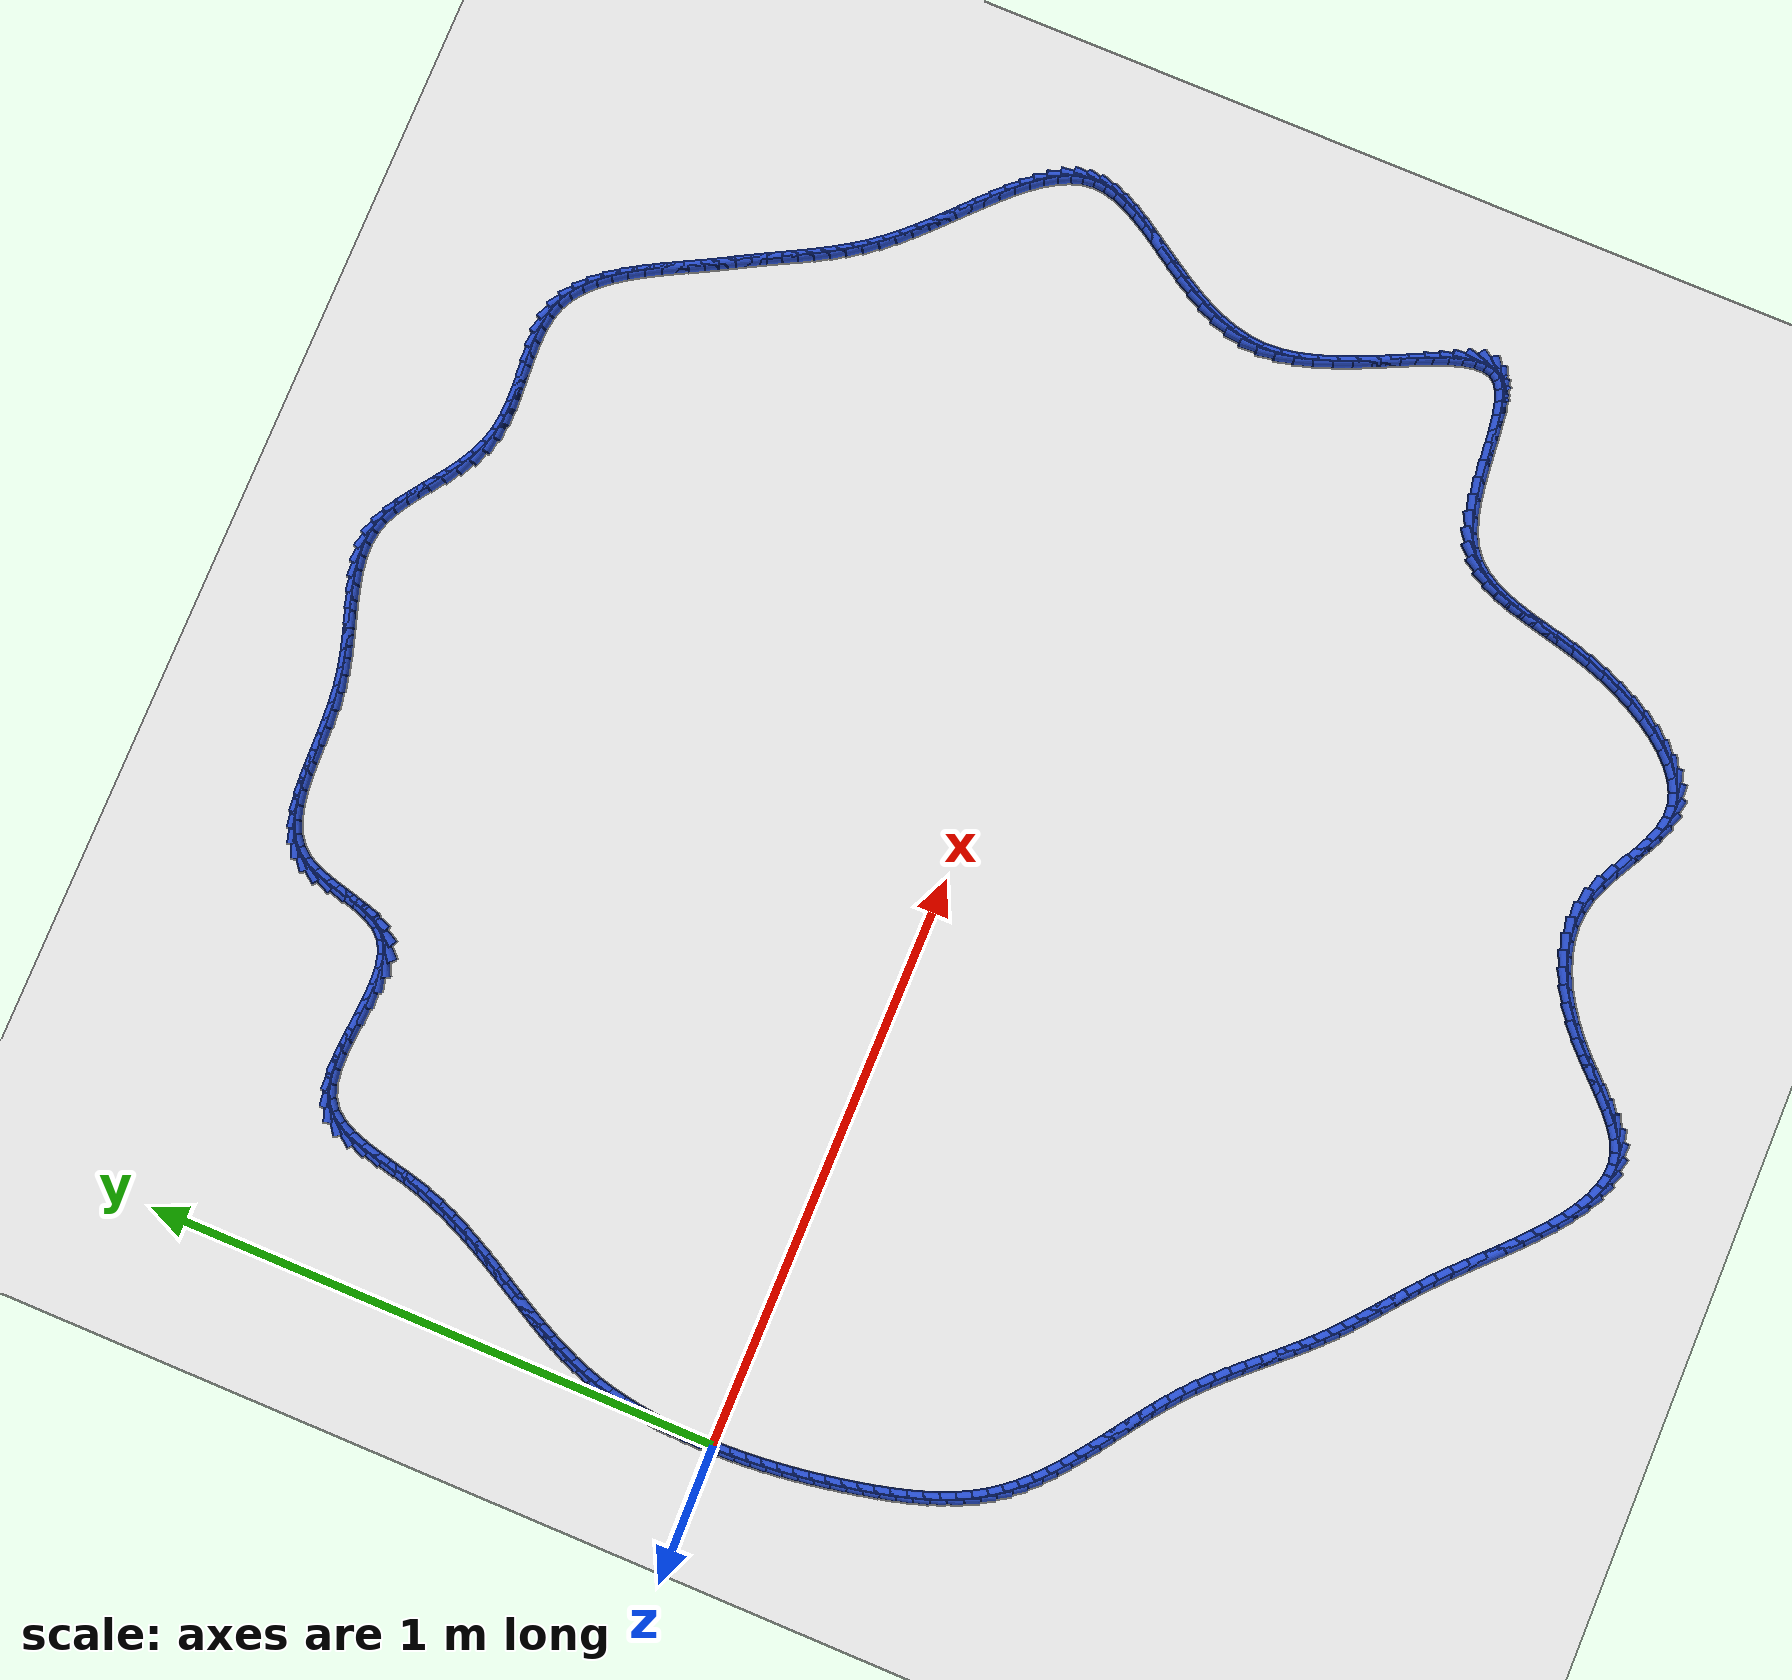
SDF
<sdf version="1.6">
 <world name="default">
  <light name="sun" type="directional">
   <pose>0 0 10 0 -0 0</pose>
   <diffuse>0.8 0.8 0.8 1</diffuse>
   <specular>0.2 0.2 0.2 1</specular>
   <attenuation>
    <range>1000</range>
    <constant>0.9</constant>
    <linear>0.01</linear>
    <quadratic>0.001</quadratic>
   </attenuation>
   <direction>-0.5 0.1 -0.9</direction>
  </light>
  <model name="ground_plane">
   <static>1</static>
   <link name="link">
    <collision name="collision">
     <geometry><plane><normal>0 0 1</normal><size>100 100</size></plane></geometry>
     <surface><friction><ode><mu>100</mu><mu2>50</mu2></ode></friction></surface>
    </collision>
    <visual name="visual">
     <cast_shadows>0</cast_shadows>
     <geometry><plane><normal>0 0 1</normal><size>100 100</size></plane></geometry>
     <material>
      <script><uri>file://media/materials/scripts/gazebo.material</uri><name>Gazebo/WhiteGlow</name></script>
     </material>
    </visual>
   </link>
  </model>
  <gravity>0 0 -9.8</gravity>
  <magnetic_field>6e-06 2.3e-05 -4.2e-05</magnetic_field>
  <atmosphere type="adiabatic"/>
  <physics name="default_physics" default="0" type="ode">
   <max_step_size>0.001</max_step_size>
   <real_time_factor>1</real_time_factor>
   <real_time_update_rate>1000</real_time_update_rate>
  </physics>
  <scene><ambient>0.4 0.4 0.4 1</ambient><background>0.7 0.7 0.7 1</background><shadows>1</shadows></scene>
  <spherical_coordinates>
   <surface_model>EARTH_WGS84</surface_model>
   <latitude_deg>0</latitude_deg>
   <longitude_deg>0</longitude_deg>
   <elevation>0</elevation>
   <heading_deg>0</heading_deg>
  </spherical_coordinates>
  <model name="line">
   <link name="link_0">
    <pose>7.806255641895632e-18 2.7755575615628914e-17 0.01 0 1.57 -1.561988760627516</pose>
    <collision name="collision">
     <geometry><cylinder><radius>0.01</radius><length>0.08</length></cylinder></geometry>
    </collision>
    <visual name="visual">
     <material>
      <script><name>Gazebo/Blue</name><uri>file://media/materials/scripts/gazebo.material</uri></script>
     </material>
     <geometry><cylinder><radius>0.01</radius><length>0.08</length></cylinder></geometry>
    </visual>
   </link>
   <link name="link_1">
    <pose>-0.00023834691809172237 0.027060909951467163 0.01 0 1.57 1.5531682049827387</pose>
    <collision name="collision">
     <geometry><cylinder><radius>0.01</radius><length>0.08</length></cylinder></geometry>
    </collision>
    <visual name="visual">
     <material>
      <script><name>Gazebo/Blue</name><uri>file://media/materials/scripts/gazebo.material</uri></script>
     </material>
     <geometry><cylinder><radius>0.01</radius><length>0.08</length></cylinder></geometry>
    </visual>
   </link>
   <link name="link_2">
    <pose>0.00024055834869044307 0.05422521390538978 0.01 0 1.57 1.5242373293625207</pose>
    <collision name="collision">
     <geometry><cylinder><radius>0.01</radius><length>0.08</length></cylinder></geometry>
    </collision>
    <visual name="visual">
     <material>
      <script><name>Gazebo/Blue</name><uri>file://media/materials/scripts/gazebo.material</uri></script>
     </material>
     <geometry><cylinder><radius>0.01</radius><length>0.08</length></cylinder></geometry>
    </visual>
   </link>
   <link name="link_3">
    <pose>0.001506280793951367 0.0813909132757816 0.01 0 1.57 1.4925489831636094</pose>
    <collision name="collision">
     <geometry><cylinder><radius>0.01</radius><length>0.08</length></cylinder></geometry>
    </collision>
    <visual name="visual">
     <material>
      <script><name>Gazebo/Blue</name><uri>file://media/materials/scripts/gazebo.material</uri></script>
     </material>
     <geometry><cylinder><radius>0.01</radius><length>0.08</length></cylinder></geometry>
    </visual>
   </link>
   <link name="link_4">
    <pose>0.0036283854112959084 0.10845600947665646 0.01 0 1.57 1.4578108943396302</pose>
    <collision name="collision">
     <geometry><cylinder><radius>0.01</radius><length>0.08</length></cylinder></geometry>
    </collision>
    <visual name="visual">
     <material>
      <script><name>Gazebo/Blue</name><uri>file://media/materials/scripts/gazebo.material</uri></script>
     </material>
     <geometry><cylinder><radius>0.01</radius><length>0.08</length></cylinder></geometry>
    </visual>
   </link>
   <link name="link_5">
    <pose>0.00667643719432893 0.13531850392202796 0.01 0 1.57 1.4197020357615828</pose>
    <collision name="collision">
     <geometry><cylinder><radius>0.01</radius><length>0.08</length></cylinder></geometry>
    </collision>
    <visual name="visual">
     <material>
      <script><name>Gazebo/Blue</name><uri>file://media/materials/scripts/gazebo.material</uri></script>
     </material>
     <geometry><cylinder><radius>0.01</radius><length>0.08</length></cylinder></geometry>
    </visual>
   </link>
   <link name="link_6">
    <pose>0.010720001136655301 0.1618763980259101 0.01 0 1.57 1.3778764237838697</pose>
    <collision name="collision">
     <geometry><cylinder><radius>0.01</radius><length>0.08</length></cylinder></geometry>
    </collision>
    <visual name="visual">
     <material>
      <script><name>Gazebo/Blue</name><uri>file://media/materials/scripts/gazebo.material</uri></script>
     </material>
     <geometry><cylinder><radius>0.01</radius><length>0.08</length></cylinder></geometry>
    </visual>
   </link>
   <link name="link_7">
    <pose>0.01582864223187988 0.18802769320231646 0.01 0 1.57 1.3319708773259131</pose>
    <collision name="collision">
     <geometry><cylinder><radius>0.01</radius><length>0.08</length></cylinder></geometry>
    </collision>
    <visual name="visual">
     <material>
      <script><name>Gazebo/Blue</name><uri>file://media/materials/scripts/gazebo.material</uri></script>
     </material>
     <geometry><cylinder><radius>0.01</radius><length>0.08</length></cylinder></geometry>
    </visual>
   </link>
   <link name="link_8">
    <pose>0.022071925473607524 0.2136703908652609 0.01 0 1.57 1.281680081722242</pose>
    <collision name="collision">
     <geometry><cylinder><radius>0.01</radius><length>0.08</length></cylinder></geometry>
    </collision>
    <visual name="visual">
     <material>
      <script><name>Gazebo/Blue</name><uri>file://media/materials/scripts/gazebo.material</uri></script>
     </material>
     <geometry><cylinder><radius>0.01</radius><length>0.08</length></cylinder></geometry>
    </visual>
   </link>
   <link name="link_9">
    <pose>0.029518110613805982 0.2387037425398303 0.01 0 1.57 1.2306982300158325</pose>
    <collision name="collision">
     <geometry><cylinder><radius>0.01</radius><length>0.08</length></cylinder></geometry>
    </collision>
    <visual name="visual">
     <material>
      <script><name>Gazebo/Blue</name><uri>file://media/materials/scripts/gazebo.material</uri></script>
     </material>
     <geometry><cylinder><radius>0.01</radius><length>0.08</length></cylinder></geometry>
    </visual>
   </link>
   <link name="link_10">
    <pose>0.03815283069181574 0.2631061364913596 0.01 0 1.57 1.1856657595457363</pose>
    <collision name="collision">
     <geometry><cylinder><radius>0.01</radius><length>0.08</length></cylinder></geometry>
    </collision>
    <visual name="visual">
     <material>
      <script><name>Gazebo/Blue</name><uri>file://media/materials/scripts/gazebo.material</uri></script>
     </material>
     <geometry><cylinder><radius>0.01</radius><length>0.08</length></cylinder></geometry>
    </visual>
   </link>
   <link name="link_11">
    <pose>0.04783110428907 0.2869810585728688 0.01 0 1.57 1.1476796684752215</pose>
    <collision name="collision">
     <geometry><cylinder><radius>0.01</radius><length>0.08</length></cylinder></geometry>
    </collision>
    <visual name="visual">
     <material>
      <script><name>Gazebo/Blue</name><uri>file://media/materials/scripts/gazebo.material</uri></script>
     </material>
     <geometry><cylinder><radius>0.01</radius><length>0.08</length></cylinder></geometry>
    </visual>
   </link>
   <link name="link_12">
    <pose>0.05839641176216312 0.31044304551273 0.01 0 1.57 1.1170740314120131</pose>
    <collision name="collision">
     <geometry><cylinder><radius>0.01</radius><length>0.08</length></cylinder></geometry>
    </collision>
    <visual name="visual">
     <material>
      <script><name>Gazebo/Blue</name><uri>file://media/materials/scripts/gazebo.material</uri></script>
     </material>
     <geometry><cylinder><radius>0.01</radius><length>0.08</length></cylinder></geometry>
    </visual>
   </link>
   <link name="link_13">
    <pose>0.06969223346768945 0.3336066340393151 0.01 0 1.57 1.0940089701561573</pose>
    <collision name="collision">
     <geometry><cylinder><radius>0.01</radius><length>0.08</length></cylinder></geometry>
    </collision>
    <visual name="visual">
     <material>
      <script><name>Gazebo/Blue</name><uri>file://media/materials/scripts/gazebo.material</uri></script>
     </material>
     <geometry><cylinder><radius>0.01</radius><length>0.08</length></cylinder></geometry>
    </visual>
   </link>
   <link name="link_14">
    <pose>0.08156204976224339 0.3565863608809963 0.01 0 1.57 1.0785171506523428</pose>
    <collision name="collision">
     <geometry><cylinder><radius>0.01</radius><length>0.08</length></cylinder></geometry>
    </collision>
    <visual name="visual">
     <material>
      <script><name>Gazebo/Blue</name><uri>file://media/materials/scripts/gazebo.material</uri></script>
     </material>
     <geometry><cylinder><radius>0.01</radius><length>0.08</length></cylinder></geometry>
    </visual>
   </link>
   <link name="link_15">
    <pose>0.09384934100241932 0.37949676276614575 0.01 0 1.57 1.070543476899343</pose>
    <collision name="collision">
     <geometry><cylinder><radius>0.01</radius><length>0.08</length></cylinder></geometry>
    </collision>
    <visual name="visual">
     <material>
      <script><name>Gazebo/Blue</name><uri>file://media/materials/scripts/gazebo.material</uri></script>
     </material>
     <geometry><cylinder><radius>0.01</radius><length>0.08</length></cylinder></geometry>
    </visual>
   </link>
   <link name="link_16">
    <pose>0.10639758754481154 0.40245237642313525 0.01 0 1.57 1.069973672523629</pose>
    <collision name="collision">
     <geometry><cylinder><radius>0.01</radius><length>0.08</length></cylinder></geometry>
    </collision>
    <visual name="visual">
     <material>
      <script><name>Gazebo/Blue</name><uri>file://media/materials/scripts/gazebo.material</uri></script>
     </material>
     <geometry><cylinder><radius>0.01</radius><length>0.08</length></cylinder></geometry>
    </visual>
   </link>
   <link name="link_17">
    <pose>0.11905026974601447 0.42556773858033703 0.01 0 1.57 1.0766503916444368</pose>
    <collision name="collision">
     <geometry><cylinder><radius>0.01</radius><length>0.08</length></cylinder></geometry>
    </collision>
    <visual name="visual">
     <material>
      <script><name>Gazebo/Blue</name><uri>file://media/materials/scripts/gazebo.material</uri></script>
     </material>
     <geometry><cylinder><radius>0.01</radius><length>0.08</length></cylinder></geometry>
    </visual>
   </link>
   <link name="link_18">
    <pose>0.13165086796262246 0.448957385966123 0.01 0 1.57 1.0903773508877337</pose>
    <collision name="collision">
     <geometry><cylinder><radius>0.01</radius><length>0.08</length></cylinder></geometry>
    </collision>
    <visual name="visual">
     <material>
      <script><name>Gazebo/Blue</name><uri>file://media/materials/scripts/gazebo.material</uri></script>
     </material>
     <geometry><cylinder><radius>0.01</radius><length>0.08</length></cylinder></geometry>
    </visual>
   </link>
   <link name="link_19">
    <pose>0.14404286255122994 0.4727358553088655 0.01 0 1.57 1.1109130738114916</pose>
    <collision name="collision">
     <geometry><cylinder><radius>0.01</radius><length>0.08</length></cylinder></geometry>
    </collision>
    <visual name="visual">
     <material>
      <script><name>Gazebo/Blue</name><uri>file://media/materials/scripts/gazebo.material</uri></script>
     </material>
     <geometry><cylinder><radius>0.01</radius><length>0.08</length></cylinder></geometry>
    </visual>
   </link>
   <link name="link_20">
    <pose>0.15606973386843118 0.4970176833369363 0.01 0 1.57 1.1379566271776875</pose>
    <collision name="collision">
     <geometry><cylinder><radius>0.01</radius><length>0.08</length></cylinder></geometry>
    </collision>
    <visual name="visual">
     <material>
      <script><name>Gazebo/Blue</name><uri>file://media/materials/scripts/gazebo.material</uri></script>
     </material>
     <geometry><cylinder><radius>0.01</radius><length>0.08</length></cylinder></geometry>
    </visual>
   </link>
   <link name="link_21">
    <pose>0.16757496227082064 0.5219174067787077 0.01 0 1.57 1.1711285279142931</pose>
    <collision name="collision">
     <geometry><cylinder><radius>0.01</radius><length>0.08</length></cylinder></geometry>
    </collision>
    <visual name="visual">
     <material>
      <script><name>Gazebo/Blue</name><uri>file://media/materials/scripts/gazebo.material</uri></script>
     </material>
     <geometry><cylinder><radius>0.01</radius><length>0.08</length></cylinder></geometry>
    </visual>
   </link>
   <link name="link_22">
    <pose>0.17840202811499267 0.5475495623625517 0.01 0 1.57 1.2099509087736775</pose>
    <collision name="collision">
     <geometry><cylinder><radius>0.01</radius><length>0.08</length></cylinder></geometry>
    </collision>
    <visual name="visual">
     <material>
      <script><name>Gazebo/Blue</name><uri>file://media/materials/scripts/gazebo.material</uri></script>
     </material>
     <geometry><cylinder><radius>0.01</radius><length>0.08</length></cylinder></geometry>
    </visual>
   </link>
   <link name="link_23">
    <pose>0.18839441175754157 0.57402868681684 0.01 0 1.57 1.2538318720527826</pose>
    <collision name="collision">
     <geometry><cylinder><radius>0.01</radius><length>0.08</length></cylinder></geometry>
    </collision>
    <visual name="visual">
     <material>
      <script><name>Gazebo/Blue</name><uri>file://media/materials/scripts/gazebo.material</uri></script>
     </material>
     <geometry><cylinder><radius>0.01</radius><length>0.08</length></cylinder></geometry>
    </visual>
   </link>
   <link name="link_24">
    <pose>0.19739559355506175 0.6014693168699451 0.01 0 1.57 1.3020434981340092</pose>
    <collision name="collision">
     <geometry><cylinder><radius>0.01</radius><length>0.08</length></cylinder></geometry>
    </collision>
    <visual name="visual">
     <material>
      <script><name>Gazebo/Blue</name><uri>file://media/materials/scripts/gazebo.material</uri></script>
     </material>
     <geometry><cylinder><radius>0.01</radius><length>0.08</length></cylinder></geometry>
    </visual>
   </link>
   <link name="link_25">
    <pose>0.20524942431371052 0.6299855744997204 0.01 0 1.57 1.343783147761084</pose>
    <collision name="collision">
     <geometry><cylinder><radius>0.01</radius><length>0.08</length></cylinder></geometry>
    </collision>
    <visual name="visual">
     <material>
      <script><name>Gazebo/Blue</name><uri>file://media/materials/scripts/gazebo.material</uri></script>
     </material>
     <geometry><cylinder><radius>0.01</radius><length>0.08</length></cylinder></geometry>
    </visual>
   </link>
   <link name="link_26">
    <pose>0.21204733430612246 0.6594143949293645 0.01 0 1.57 1.353040288297044</pose>
    <collision name="collision">
     <geometry><cylinder><radius>0.01</radius><length>0.08</length></cylinder></geometry>
    </collision>
    <visual name="visual">
     <material>
      <script><name>Gazebo/Blue</name><uri>file://media/materials/scripts/gazebo.material</uri></script>
     </material>
     <geometry><cylinder><radius>0.01</radius><length>0.08</length></cylinder></geometry>
    </visual>
   </link>
   <link name="link_27">
    <pose>0.21855716005840817 0.688835417727082 0.01 0 1.57 1.3253910439511205</pose>
    <collision name="collision">
     <geometry><cylinder><radius>0.01</radius><length>0.08</length></cylinder></geometry>
    </collision>
    <visual name="visual">
     <material>
      <script><name>Gazebo/Blue</name><uri>file://media/materials/scripts/gazebo.material</uri></script>
     </material>
     <geometry><cylinder><radius>0.01</radius><length>0.08</length></cylinder></geometry>
    </visual>
   </link>
   <link name="link_28">
    <pose>0.22566119793408768 0.7172001347139273 0.01 0 1.57 1.2549781935807882</pose>
    <collision name="collision">
     <geometry><cylinder><radius>0.01</radius><length>0.08</length></cylinder></geometry>
    </collision>
    <visual name="visual">
     <material>
      <script><name>Gazebo/Blue</name><uri>file://media/materials/scripts/gazebo.material</uri></script>
     </material>
     <geometry><cylinder><radius>0.01</radius><length>0.08</length></cylinder></geometry>
    </visual>
   </link>
   <link name="link_29">
    <pose>0.2342417442966808 0.7434600377109538 0.01 0 1.57 1.1286296549307193</pose>
    <collision name="collision">
     <geometry><cylinder><radius>0.01</radius><length>0.08</length></cylinder></geometry>
    </collision>
    <visual name="visual">
     <material>
      <script><name>Gazebo/Blue</name><uri>file://media/materials/scripts/gazebo.material</uri></script>
     </material>
     <geometry><cylinder><radius>0.01</radius><length>0.08</length></cylinder></geometry>
    </visual>
   </link>
   <link name="link_30">
    <pose>0.2451810955097074 0.7665666185392155 0.01 0 1.57 0.9272312518262499</pose>
    <collision name="collision">
     <geometry><cylinder><radius>0.01</radius><length>0.08</length></cylinder></geometry>
    </collision>
    <visual name="visual">
     <material>
      <script><name>Gazebo/Blue</name><uri>file://media/materials/scripts/gazebo.material</uri></script>
     </material>
     <geometry><cylinder><radius>0.01</radius><length>0.08</length></cylinder></geometry>
    </visual>
   </link>
   <link name="link_31">
    <pose>0.25936154793668753 0.7854713690197663 0.01 0 1.57 0.6419037195079508</pose>
    <collision name="collision">
     <geometry><cylinder><radius>0.01</radius><length>0.08</length></cylinder></geometry>
    </collision>
    <visual name="visual">
     <material>
      <script><name>Gazebo/Blue</name><uri>file://media/materials/scripts/gazebo.material</uri></script>
     </material>
     <geometry><cylinder><radius>0.01</radius><length>0.08</length></cylinder></geometry>
    </visual>
   </link>
   <link name="link_32">
    <pose>0.2776513134428089 0.7991430979301705 0.01 0 1.57 0.35094569051930663</pose>
    <collision name="collision">
     <geometry><cylinder><radius>0.01</radius><length>0.08</length></cylinder></geometry>
    </collision>
    <visual name="visual">
     <material>
      <script><name>Gazebo/Blue</name><uri>file://media/materials/scripts/gazebo.material</uri></script>
     </material>
     <geometry><cylinder><radius>0.01</radius><length>0.08</length></cylinder></geometry>
    </visual>
   </link>
   <link name="link_33">
    <pose>0.30022253444139285 0.8074064346914842 0.01 0 1.57 0.14914194250032858</pose>
    <collision name="collision">
     <geometry><cylinder><radius>0.01</radius><length>0.08</length></cylinder></geometry>
    </collision>
    <visual name="visual">
     <material>
      <script><name>Gazebo/Blue</name><uri>file://media/materials/scripts/gazebo.material</uri></script>
     </material>
     <geometry><cylinder><radius>0.01</radius><length>0.08</length></cylinder></geometry>
    </visual>
   </link>
   <link name="link_34">
    <pose>0.32624637487104396 0.8113167164365551 0.01 0 1.57 0.024775238561189537</pose>
    <collision name="collision">
     <geometry><cylinder><radius>0.01</radius><length>0.08</length></cylinder></geometry>
    </collision>
    <visual name="visual">
     <material>
      <script><name>Gazebo/Blue</name><uri>file://media/materials/scripts/gazebo.material</uri></script>
     </material>
     <geometry><cylinder><radius>0.01</radius><length>0.08</length></cylinder></geometry>
    </visual>
   </link>
   <link name="link_35">
    <pose>0.35481639819885447 0.8120246904405466 0.01 0 1.57 -0.04444594028672494</pose>
    <collision name="collision">
     <geometry><cylinder><radius>0.01</radius><length>0.08</length></cylinder></geometry>
    </collision>
    <visual name="visual">
     <material>
      <script><name>Gazebo/Blue</name><uri>file://media/materials/scripts/gazebo.material</uri></script>
     </material>
     <geometry><cylinder><radius>0.01</radius><length>0.08</length></cylinder></geometry>
    </visual>
   </link>
   <link name="link_36">
    <pose>0.3850261678919171 0.8106811039786226 0.01 0 1.57 -0.07240636971673417</pose>
    <collision name="collision">
     <geometry><cylinder><radius>0.01</radius><length>0.08</length></cylinder></geometry>
    </collision>
    <visual name="visual">
     <material>
      <script><name>Gazebo/Blue</name><uri>file://media/materials/scripts/gazebo.material</uri></script>
     </material>
     <geometry><cylinder><radius>0.01</radius><length>0.08</length></cylinder></geometry>
    </visual>
   </link>
   <link name="link_37">
    <pose>0.4159692474173244 0.8084367043259473 0.01 0 1.57 -0.06472806060632869</pose>
    <collision name="collision">
     <geometry><cylinder><radius>0.01</radius><length>0.08</length></cylinder></geometry>
    </collision>
    <visual name="visual">
     <material>
      <script><name>Gazebo/Blue</name><uri>file://media/materials/scripts/gazebo.material</uri></script>
     </material>
     <geometry><cylinder><radius>0.01</radius><length>0.08</length></cylinder></geometry>
    </visual>
   </link>
   <link name="link_38">
    <pose>0.4467392002421685 0.8064422387576843 0.01 0 1.57 -0.019996539988555044</pose>
    <collision name="collision">
     <geometry><cylinder><radius>0.01</radius><length>0.08</length></cylinder></geometry>
    </collision>
    <visual name="visual">
     <material>
      <script><name>Gazebo/Blue</name><uri>file://media/materials/scripts/gazebo.material</uri></script>
     </material>
     <geometry><cylinder><radius>0.01</radius><length>0.08</length></cylinder></geometry>
    </visual>
   </link>
   <link name="link_39">
    <pose>0.4764295898335419 0.8058484545489979 0.01 0 1.57 0.07054462940587654</pose>
    <collision name="collision">
     <geometry><cylinder><radius>0.01</radius><length>0.08</length></cylinder></geometry>
    </collision>
    <visual name="visual">
     <material>
      <script><name>Gazebo/Blue</name><uri>file://media/materials/scripts/gazebo.material</uri></script>
     </material>
     <geometry><cylinder><radius>0.01</radius><length>0.08</length></cylinder></geometry>
    </visual>
   </link>
   <link name="link_40">
    <pose>0.504133979658537 0.8078060989750518 0.01 0 1.57 0.2242712890571143</pose>
    <collision name="collision">
     <geometry><cylinder><radius>0.01</radius><length>0.08</length></cylinder></geometry>
    </collision>
    <visual name="visual">
     <material>
      <script><name>Gazebo/Blue</name><uri>file://media/materials/scripts/gazebo.material</uri></script>
     </material>
     <geometry><cylinder><radius>0.01</radius><length>0.08</length></cylinder></geometry>
    </visual>
   </link>
   <link name="link_41">
    <pose>0.5289459331842464 0.8134659193110099 0.01 0 1.57 0.46388374540919725</pose>
    <collision name="collision">
     <geometry><cylinder><radius>0.01</radius><length>0.08</length></cylinder></geometry>
    </collision>
    <visual name="visual">
     <material>
      <script><name>Gazebo/Blue</name><uri>file://media/materials/scripts/gazebo.material</uri></script>
     </material>
     <geometry><cylinder><radius>0.01</radius><length>0.08</length></cylinder></geometry>
    </visual>
   </link>
   <link name="link_42">
    <pose>0.5499590138777626 0.8239786628320361 0.01 0 1.57 0.7879435264150362</pose>
    <collision name="collision">
     <geometry><cylinder><radius>0.01</radius><length>0.08</length></cylinder></geometry>
    </collision>
    <visual name="visual">
     <material>
      <script><name>Gazebo/Blue</name><uri>file://media/materials/scripts/gazebo.material</uri></script>
     </material>
     <geometry><cylinder><radius>0.01</radius><length>0.08</length></cylinder></geometry>
    </visual>
   </link>
   <link name="link_43">
    <pose>0.5663218166258303 0.8404249768729714 0.01 0 1.57 1.0715326450406237</pose>
    <collision name="collision">
     <geometry><cylinder><radius>0.01</radius><length>0.08</length></cylinder></geometry>
    </collision>
    <visual name="visual">
     <material>
      <script><name>Gazebo/Blue</name><uri>file://media/materials/scripts/gazebo.material</uri></script>
     </material>
     <geometry><cylinder><radius>0.01</radius><length>0.08</length></cylinder></geometry>
    </visual>
   </link>
   <link name="link_44">
    <pose>0.5783235738967009 0.8624325455905482 0.01 0 1.57 1.2353045468312742</pose>
    <collision name="collision">
     <geometry><cylinder><radius>0.01</radius><length>0.08</length></cylinder></geometry>
    </collision>
    <visual name="visual">
     <material>
      <script><name>Gazebo/Blue</name><uri>file://media/materials/scripts/gazebo.material</uri></script>
     </material>
     <geometry><cylinder><radius>0.01</radius><length>0.08</length></cylinder></geometry>
    </visual>
   </link>
   <link name="link_45">
    <pose>0.5873287096634411 0.8882594562675766 0.01 0 1.57 1.3105978796279953</pose>
    <collision name="collision">
     <geometry><cylinder><radius>0.01</radius><length>0.08</length></cylinder></geometry>
    </collision>
    <visual name="visual">
     <material>
      <script><name>Gazebo/Blue</name><uri>file://media/materials/scripts/gazebo.material</uri></script>
     </material>
     <geometry><cylinder><radius>0.01</radius><length>0.08</length></cylinder></geometry>
    </visual>
   </link>
   <link name="link_46">
    <pose>0.5947435757755332 0.916110387758495 0.01 0 1.57 1.3187565866261128</pose>
    <collision name="collision">
     <geometry><cylinder><radius>0.01</radius><length>0.08</length></cylinder></geometry>
    </collision>
    <visual name="visual">
     <material>
      <script><name>Gazebo/Blue</name><uri>file://media/materials/scripts/gazebo.material</uri></script>
     </material>
     <geometry><cylinder><radius>0.01</radius><length>0.08</length></cylinder></geometry>
    </visual>
   </link>
   <link name="link_47">
    <pose>0.6019745240824607 0.944190018917742 0.01 0 1.57 1.2621468643064853</pose>
    <collision name="collision">
     <geometry><cylinder><radius>0.01</radius><length>0.08</length></cylinder></geometry>
    </collision>
    <visual name="visual">
     <material>
      <script><name>Gazebo/Blue</name><uri>file://media/materials/scripts/gazebo.material</uri></script>
     </material>
     <geometry><cylinder><radius>0.01</radius><length>0.08</length></cylinder></geometry>
    </visual>
   </link>
   <link name="link_48">
    <pose>0.6104279064337065 0.9707030285997563 0.01 0 1.57 1.1243421539087712</pose>
    <collision name="collision">
     <geometry><cylinder><radius>0.01</radius><length>0.08</length></cylinder></geometry>
    </collision>
    <visual name="visual">
     <material>
      <script><name>Gazebo/Blue</name><uri>file://media/materials/scripts/gazebo.material</uri></script>
     </material>
     <geometry><cylinder><radius>0.01</radius><length>0.08</length></cylinder></geometry>
    </visual>
   </link>
   <link name="link_49">
    <pose>0.6215100746787533 0.9938540956589759 0.01 0 1.57 0.892775921830412</pose>
    <collision name="collision">
     <geometry><cylinder><radius>0.01</radius><length>0.08</length></cylinder></geometry>
    </collision>
    <visual name="visual">
     <material>
      <script><name>Gazebo/Blue</name><uri>file://media/materials/scripts/gazebo.material</uri></script>
     </material>
     <geometry><cylinder><radius>0.01</radius><length>0.08</length></cylinder></geometry>
    </visual>
   </link>
   <link name="link_50">
    <pose>0.6363256004482516 1.0122495066304722 0.01 0 1.57 0.6462603727124178</pose>
    <collision name="collision">
     <geometry><cylinder><radius>0.01</radius><length>0.08</length></cylinder></geometry>
    </collision>
    <visual name="visual">
     <material>
      <script><name>Gazebo/Blue</name><uri>file://media/materials/scripts/gazebo.material</uri></script>
     </material>
     <geometry><cylinder><radius>0.01</radius><length>0.08</length></cylinder></geometry>
    </visual>
   </link>
   <link name="link_51">
    <pose>0.6547422133053874 1.0261415315930502 0.01 0 1.57 0.43652000357089554</pose>
    <collision name="collision">
     <geometry><cylinder><radius>0.01</radius><length>0.08</length></cylinder></geometry>
    </collision>
    <visual name="visual">
     <material>
      <script><name>Gazebo/Blue</name><uri>file://media/materials/scripts/gazebo.material</uri></script>
     </material>
     <geometry><cylinder><radius>0.01</radius><length>0.08</length></cylinder></geometry>
    </visual>
   </link>
   <link name="link_52">
    <pose>0.6763108199644118 1.0362040669667771 0.01 0 1.57 0.277241402589457</pose>
    <collision name="collision">
     <geometry><cylinder><radius>0.01</radius><length>0.08</length></cylinder></geometry>
    </collision>
    <visual name="visual">
     <material>
      <script><name>Gazebo/Blue</name><uri>file://media/materials/scripts/gazebo.material</uri></script>
     </material>
     <geometry><cylinder><radius>0.01</radius><length>0.08</length></cylinder></geometry>
    </visual>
   </link>
   <link name="link_53">
    <pose>0.7005823269747773 1.0431110093910356 0.01 0 1.57 0.16530861892790447</pose>
    <collision name="collision">
     <geometry><cylinder><radius>0.01</radius><length>0.08</length></cylinder></geometry>
    </collision>
    <visual name="visual">
     <material>
      <script><name>Gazebo/Blue</name><uri>file://media/materials/scripts/gazebo.material</uri></script>
     </material>
     <geometry><cylinder><radius>0.01</radius><length>0.08</length></cylinder></geometry>
    </visual>
   </link>
   <link name="link_54">
    <pose>0.727107640885937 1.0475362555052066 0.01 0 1.57 0.09212969307171853</pose>
    <collision name="collision">
     <geometry><cylinder><radius>0.01</radius><length>0.08</length></cylinder></geometry>
    </collision>
    <visual name="visual">
     <material>
      <script><name>Gazebo/Blue</name><uri>file://media/materials/scripts/gazebo.material</uri></script>
     </material>
     <geometry><cylinder><radius>0.01</radius><length>0.08</length></cylinder></geometry>
    </visual>
   </link>
   <link name="link_55">
    <pose>0.7554376682473433 1.050153701948671 0.01 0 1.57 0.04993356506762568</pose>
    <collision name="collision">
     <geometry><cylinder><radius>0.01</radius><length>0.08</length></cylinder></geometry>
    </collision>
    <visual name="visual">
     <material>
      <script><name>Gazebo/Blue</name><uri>file://media/materials/scripts/gazebo.material</uri></script>
     </material>
     <geometry><cylinder><radius>0.01</radius><length>0.08</length></cylinder></geometry>
    </visual>
   </link>
   <link name="link_56">
    <pose>0.7851233156084486 1.0516372453608107 0.01 0 1.57 0.033445003376697306</pose>
    <collision name="collision">
     <geometry><cylinder><radius>0.01</radius><length>0.08</length></cylinder></geometry>
    </collision>
    <visual name="visual">
     <material>
      <script><name>Gazebo/Blue</name><uri>file://media/materials/scripts/gazebo.material</uri></script>
     </material>
     <geometry><cylinder><radius>0.01</radius><length>0.08</length></cylinder></geometry>
    </visual>
   </link>
   <link name="link_57">
    <pose>0.8157154895187055 1.0526607823810064 0.01 0 1.57 0.039832155162960334</pose>
    <collision name="collision">
     <geometry><cylinder><radius>0.01</radius><length>0.08</length></cylinder></geometry>
    </collision>
    <visual name="visual">
     <material>
      <script><name>Gazebo/Blue</name><uri>file://media/materials/scripts/gazebo.material</uri></script>
     </material>
     <geometry><cylinder><radius>0.01</radius><length>0.08</length></cylinder></geometry>
    </visual>
   </link>
   <link name="link_58">
    <pose>0.8467650965275674 1.05389820964864 0.01 0 1.57 0.06832088730275097</pose>
    <collision name="collision">
     <geometry><cylinder><radius>0.01</radius><length>0.08</length></cylinder></geometry>
    </collision>
    <visual name="visual">
     <material>
      <script><name>Gazebo/Blue</name><uri>file://media/materials/scripts/gazebo.material</uri></script>
     </material>
     <geometry><cylinder><radius>0.01</radius><length>0.08</length></cylinder></geometry>
    </visual>
   </link>
   <link name="link_59">
    <pose>0.8778230431844865 1.0560234238030923 0.01 0 1.57 0.11984214740603137</pose>
    <collision name="collision">
     <geometry><cylinder><radius>0.01</radius><length>0.08</length></cylinder></geometry>
    </collision>
    <visual name="visual">
     <material>
      <script><name>Gazebo/Blue</name><uri>file://media/materials/scripts/gazebo.material</uri></script>
     </material>
     <geometry><cylinder><radius>0.01</radius><length>0.08</length></cylinder></geometry>
    </visual>
   </link>
   <link name="link_60">
    <pose>0.9084402360524533 1.0597103214474983 0.01 0 1.57 0.18898064070990592</pose>
    <collision name="collision">
     <geometry><cylinder><radius>0.01</radius><length>0.08</length></cylinder></geometry>
    </collision>
    <visual name="visual">
     <material>
      <script><name>Gazebo/Blue</name><uri>file://media/materials/scripts/gazebo.material</uri></script>
     </material>
     <geometry><cylinder><radius>0.01</radius><length>0.08</length></cylinder></geometry>
    </visual>
   </link>
   <link name="link_61">
    <pose>0.938250105020642 1.0654118458831983 0.01 0 1.57 0.2469142991239599</pose>
    <collision name="collision">
     <geometry><cylinder><radius>0.01</radius><length>0.08</length></cylinder></geometry>
    </collision>
    <visual name="visual">
     <material>
      <script><name>Gazebo/Blue</name><uri>file://media/materials/scripts/gazebo.material</uri></script>
     </material>
     <geometry><cylinder><radius>0.01</radius><length>0.08</length></cylinder></geometry>
    </visual>
   </link>
   <link name="link_62">
    <pose>0.9672107673984187 1.0727116012699862 0.01 0 1.57 0.28567785501170184</pose>
    <collision name="collision">
     <geometry><cylinder><radius>0.01</radius><length>0.08</length></cylinder></geometry>
    </collision>
    <visual name="visual">
     <material>
      <script><name>Gazebo/Blue</name><uri>file://media/materials/scripts/gazebo.material</uri></script>
     </material>
     <geometry><cylinder><radius>0.01</radius><length>0.08</length></cylinder></geometry>
    </visual>
   </link>
   <link name="link_63">
    <pose>0.9953601829395751 1.080979416432428 0.01 0 1.57 0.30456997993642676</pose>
    <collision name="collision">
     <geometry><cylinder><radius>0.01</radius><length>0.08</length></cylinder></geometry>
    </collision>
    <visual name="visual">
     <material>
      <script><name>Gazebo/Blue</name><uri>file://media/materials/scripts/gazebo.material</uri></script>
     </material>
     <geometry><cylinder><radius>0.01</radius><length>0.08</length></cylinder></geometry>
    </visual>
   </link>
   <link name="link_64">
    <pose>1.0227363113979027 1.089585120195091 0.01 0 1.57 0.3024802968139713</pose>
    <collision name="collision">
     <geometry><cylinder><radius>0.01</radius><length>0.08</length></cylinder></geometry>
    </collision>
    <visual name="visual">
     <material>
      <script><name>Gazebo/Blue</name><uri>file://media/materials/scripts/gazebo.material</uri></script>
     </material>
     <geometry><cylinder><radius>0.01</radius><length>0.08</length></cylinder></geometry>
    </visual>
   </link>
   <link name="link_65">
    <pose>1.0493771125271925 1.097898541382541 0.01 0 1.57 0.2775353731377268</pose>
    <collision name="collision">
     <geometry><cylinder><radius>0.01</radius><length>0.08</length></cylinder></geometry>
    </collision>
    <visual name="visual">
     <material>
      <script><name>Gazebo/Blue</name><uri>file://media/materials/scripts/gazebo.material</uri></script>
     </material>
     <geometry><cylinder><radius>0.01</radius><length>0.08</length></cylinder></geometry>
    </visual>
   </link>
   <link name="link_66">
    <pose>1.075320546081236 1.105289508819345 0.01 0 1.57 0.2269328008418897</pose>
    <collision name="collision">
     <geometry><cylinder><radius>0.01</radius><length>0.08</length></cylinder></geometry>
    </collision>
    <visual name="visual">
     <material>
      <script><name>Gazebo/Blue</name><uri>file://media/materials/scripts/gazebo.material</uri></script>
     </material>
     <geometry><cylinder><radius>0.01</radius><length>0.08</length></cylinder></geometry>
    </visual>
   </link>
   <link name="link_67">
    <pose>1.1006045718138247 1.1111278513300695 0.01 0 1.57 0.1471510101023588</pose>
    <collision name="collision">
     <geometry><cylinder><radius>0.01</radius><length>0.08</length></cylinder></geometry>
    </collision>
    <visual name="visual">
     <material>
      <script><name>Gazebo/Blue</name><uri>file://media/materials/scripts/gazebo.material</uri></script>
     </material>
     <geometry><cylinder><radius>0.01</radius><length>0.08</length></cylinder></geometry>
    </visual>
   </link>
   <link name="link_68">
    <pose>1.1252671494787498 1.1147833977392805 0.01 0 1.57 0.034977879502217556</pose>
    <collision name="collision">
     <geometry><cylinder><radius>0.01</radius><length>0.08</length></cylinder></geometry>
    </collision>
    <visual name="visual">
     <material>
      <script><name>Gazebo/Blue</name><uri>file://media/materials/scripts/gazebo.material</uri></script>
     </material>
     <geometry><cylinder><radius>0.01</radius><length>0.08</length></cylinder></geometry>
    </visual>
   </link>
   <link name="link_69">
    <pose>1.1493462388298028 1.1156259768715449 0.01 0 1.57 -0.11005775600568005</pose>
    <collision name="collision">
     <geometry><cylinder><radius>0.01</radius><length>0.08</length></cylinder></geometry>
    </collision>
    <visual name="visual">
     <material>
      <script><name>Gazebo/Blue</name><uri>file://media/materials/scripts/gazebo.material</uri></script>
     </material>
     <geometry><cylinder><radius>0.01</radius><length>0.08</length></cylinder></geometry>
    </visual>
   </link>
   <link name="link_70">
    <pose>1.1728797996207747 1.1130254175514291 0.01 0 1.57 -0.27997357270882256</pose>
    <collision name="collision">
     <geometry><cylinder><radius>0.01</radius><length>0.08</length></cylinder></geometry>
    </collision>
    <visual name="visual">
     <material>
      <script><name>Gazebo/Blue</name><uri>file://media/materials/scripts/gazebo.material</uri></script>
     </material>
     <geometry><cylinder><radius>0.01</radius><length>0.08</length></cylinder></geometry>
    </visual>
   </link>
   <link name="link_71">
    <pose>1.1959105733230002 1.1064034779111185 0.01 0 1.57 -0.4302138245966116</pose>
    <collision name="collision">
     <geometry><cylinder><radius>0.01</radius><length>0.08</length></cylinder></geometry>
    </collision>
    <visual name="visual">
     <material>
      <script><name>Gazebo/Blue</name><uri>file://media/materials/scripts/gazebo.material</uri></script>
     </material>
     <geometry><cylinder><radius>0.01</radius><length>0.08</length></cylinder></geometry>
    </visual>
   </link>
   <link name="link_72">
    <pose>1.218557661602768 1.096011185486182 0.01 0 1.57 -0.5331513210577749</pose>
    <collision name="collision">
     <geometry><cylinder><radius>0.01</radius><length>0.08</length></cylinder></geometry>
    </collision>
    <visual name="visual">
     <material>
      <script><name>Gazebo/Blue</name><uri>file://media/materials/scripts/gazebo.material</uri></script>
     </material>
     <geometry><cylinder><radius>0.01</radius><length>0.08</length></cylinder></geometry>
    </visual>
   </link>
   <link name="link_73">
    <pose>1.2410015106871914 1.0827657678838842 0.01 0 1.57 -0.5945797289183539</pose>
    <collision name="collision">
     <geometry><cylinder><radius>0.01</radius><length>0.08</length></cylinder></geometry>
    </collision>
    <visual name="visual">
     <material>
      <script><name>Gazebo/Blue</name><uri>file://media/materials/scripts/gazebo.material</uri></script>
     </material>
     <geometry><cylinder><radius>0.01</radius><length>0.08</length></cylinder></geometry>
    </visual>
   </link>
   <link name="link_74">
    <pose>1.2634243001894285 1.0676032772314312 0.01 0 1.57 -0.620605564729072</pose>
    <collision name="collision">
     <geometry><cylinder><radius>0.01</radius><length>0.08</length></cylinder></geometry>
    </collision>
    <visual name="visual">
     <material>
      <script><name>Gazebo/Blue</name><uri>file://media/materials/scripts/gazebo.material</uri></script>
     </material>
     <geometry><cylinder><radius>0.01</radius><length>0.08</length></cylinder></geometry>
    </visual>
   </link>
   <link name="link_75">
    <pose>1.2860082097226389 1.0514597656560314 0.01 0 1.57 -0.6147959192971442</pose>
    <collision name="collision">
     <geometry><cylinder><radius>0.01</radius><length>0.08</length></cylinder></geometry>
    </collision>
    <visual name="visual">
     <material>
      <script><name>Gazebo/Blue</name><uri>file://media/materials/scripts/gazebo.material</uri></script>
     </material>
     <geometry><cylinder><radius>0.01</radius><length>0.08</length></cylinder></geometry>
    </visual>
   </link>
   <link name="link_76">
    <pose>1.308935418899981 1.0352712852848913 0.01 0 1.57 -0.5779667141186224</pose>
    <collision name="collision">
     <geometry><cylinder><radius>0.01</radius><length>0.08</length></cylinder></geometry>
    </collision>
    <visual name="visual">
     <material>
      <script><name>Gazebo/Blue</name><uri>file://media/materials/scripts/gazebo.material</uri></script>
     </material>
     <geometry><cylinder><radius>0.01</radius><length>0.08</length></cylinder></geometry>
    </visual>
   </link>
   <link name="link_77">
    <pose>1.3323881073346138 1.019973888245218 0.01 0 1.57 -0.5086105331560083</pose>
    <collision name="collision">
     <geometry><cylinder><radius>0.01</radius><length>0.08</length></cylinder></geometry>
    </collision>
    <visual name="visual">
     <material>
      <script><name>Gazebo/Blue</name><uri>file://media/materials/scripts/gazebo.material</uri></script>
     </material>
     <geometry><cylinder><radius>0.01</radius><length>0.08</length></cylinder></geometry>
    </visual>
   </link>
   <link name="link_78">
    <pose>1.3565484546396964 1.006503626664219 0.01 0 1.57 -0.4039227936931797</pose>
    <collision name="collision">
     <geometry><cylinder><radius>0.01</radius><length>0.08</length></cylinder></geometry>
    </collision>
    <visual name="visual">
     <material>
      <script><name>Gazebo/Blue</name><uri>file://media/materials/scripts/gazebo.material</uri></script>
     </material>
     <geometry><cylinder><radius>0.01</radius><length>0.08</length></cylinder></geometry>
    </visual>
   </link>
   <link name="link_79">
    <pose>1.3815986404283878 0.9957965526691019 0.01 0 1.57 -0.26442928315448877</pose>
    <collision name="collision">
     <geometry><cylinder><radius>0.01</radius><length>0.08</length></cylinder></geometry>
    </collision>
    <visual name="visual">
     <material>
      <script><name>Gazebo/Blue</name><uri>file://media/materials/scripts/gazebo.material</uri></script>
     </material>
     <geometry><cylinder><radius>0.01</radius><length>0.08</length></cylinder></geometry>
    </visual>
   </link>
   <link name="link_80">
    <pose>1.407704253547178 0.9887279384162144 0.01 0 1.57 -0.12939909151889062</pose>
    <collision name="collision">
     <geometry><cylinder><radius>0.01</radius><length>0.08</length></cylinder></geometry>
    </collision>
    <visual name="visual">
     <material>
      <script><name>Gazebo/Blue</name><uri>file://media/materials/scripts/gazebo.material</uri></script>
     </material>
     <geometry><cylinder><radius>0.01</radius><length>0.08</length></cylinder></geometry>
    </visual>
   </link>
   <link name="link_81">
    <pose>1.43476701063288 0.98520636503817 0.01 0 1.57 -0.030323236224047437</pose>
    <collision name="collision">
     <geometry><cylinder><radius>0.01</radius><length>0.08</length></cylinder></geometry>
    </collision>
    <visual name="visual">
     <material>
      <script><name>Gazebo/Blue</name><uri>file://media/materials/scripts/gazebo.material</uri></script>
     </material>
     <geometry><cylinder><radius>0.01</radius><length>0.08</length></cylinder></geometry>
    </visual>
   </link>
   <link name="link_82">
    <pose>1.4624771986239995 0.9843658448270413 0.01 0 1.57 0.03396394064905525</pose>
    <collision name="collision">
     <geometry><cylinder><radius>0.01</radius><length>0.08</length></cylinder></geometry>
    </collision>
    <visual name="visual">
     <material>
      <script><name>Gazebo/Blue</name><uri>file://media/materials/scripts/gazebo.material</uri></script>
     </material>
     <geometry><cylinder><radius>0.01</radius><length>0.08</length></cylinder></geometry>
    </visual>
   </link>
   <link name="link_83">
    <pose>1.4905191638764683 0.9853186268590738 0.01 0 1.57 0.06613505344259576</pose>
    <collision name="collision">
     <geometry><cylinder><radius>0.01</radius><length>0.08</length></cylinder></geometry>
    </collision>
    <visual name="visual">
     <material>
      <script><name>Gazebo/Blue</name><uri>file://media/materials/scripts/gazebo.material</uri></script>
     </material>
     <geometry><cylinder><radius>0.01</radius><length>0.08</length></cylinder></geometry>
    </visual>
   </link>
   <link name="link_84">
    <pose>1.518577252746221 0.9871769602105155 0.01 0 1.57 0.0674849434901481</pose>
    <collision name="collision">
     <geometry><cylinder><radius>0.01</radius><length>0.08</length></cylinder></geometry>
    </collision>
    <visual name="visual">
     <material>
      <script><name>Gazebo/Blue</name><uri>file://media/materials/scripts/gazebo.material</uri></script>
     </material>
     <geometry><cylinder><radius>0.01</radius><length>0.08</length></cylinder></geometry>
    </visual>
   </link>
   <link name="link_85">
    <pose>1.5463358115891888 0.989053093957612 0.01 0 1.57 0.037052235330977436</pose>
    <collision name="collision">
     <geometry><cylinder><radius>0.01</radius><length>0.08</length></cylinder></geometry>
    </collision>
    <visual name="visual">
     <material>
      <script><name>Gazebo/Blue</name><uri>file://media/materials/scripts/gazebo.material</uri></script>
     </material>
     <geometry><cylinder><radius>0.01</radius><length>0.08</length></cylinder></geometry>
    </visual>
   </link>
   <link name="link_86">
    <pose>1.573479186761305 0.9900592771766102 0.01 0 1.57 -0.02866233050834766</pose>
    <collision name="collision">
     <geometry><cylinder><radius>0.01</radius><length>0.08</length></cylinder></geometry>
    </collision>
    <visual name="visual">
     <material>
      <script><name>Gazebo/Blue</name><uri>file://media/materials/scripts/gazebo.material</uri></script>
     </material>
     <geometry><cylinder><radius>0.01</radius><length>0.08</length></cylinder></geometry>
    </visual>
   </link>
   <link name="link_87">
    <pose>1.5996917246185023 0.9893077589437574 0.01 0 1.57 -0.13523315846179806</pose>
    <collision name="collision">
     <geometry><cylinder><radius>0.01</radius><length>0.08</length></cylinder></geometry>
    </collision>
    <visual name="visual">
     <material>
      <script><name>Gazebo/Blue</name><uri>file://media/materials/scripts/gazebo.material</uri></script>
     </material>
     <geometry><cylinder><radius>0.01</radius><length>0.08</length></cylinder></geometry>
    </visual>
   </link>
   <link name="link_88">
    <pose>1.624657771516713 0.9859107883352992 0.01 0 1.57 -0.2878669561494022</pose>
    <collision name="collision">
     <geometry><cylinder><radius>0.01</radius><length>0.08</length></cylinder></geometry>
    </collision>
    <visual name="visual">
     <material>
      <script><name>Gazebo/Blue</name><uri>file://media/materials/scripts/gazebo.material</uri></script>
     </material>
     <geometry><cylinder><radius>0.01</radius><length>0.08</length></cylinder></geometry>
    </visual>
   </link>
   <link name="link_89">
    <pose>1.6480618248279584 0.9789810524919115 0.01 0 1.57 -0.4708287167649854</pose>
    <collision name="collision">
     <geometry><cylinder><radius>0.01</radius><length>0.08</length></cylinder></geometry>
    </collision>
    <visual name="visual">
     <material>
      <script><name>Gazebo/Blue</name><uri>file://media/materials/scripts/gazebo.material</uri></script>
     </material>
     <geometry><cylinder><radius>0.01</radius><length>0.08</length></cylinder></geometry>
    </visual>
   </link>
   <link name="link_90">
    <pose>1.6697035225113004 0.9679652360531033 0.01 0 1.57 -0.6347008481589415</pose>
    <collision name="collision">
     <geometry><cylinder><radius>0.01</radius><length>0.08</length></cylinder></geometry>
    </collision>
    <visual name="visual">
     <material>
      <script><name>Gazebo/Blue</name><uri>file://media/materials/scripts/gazebo.material</uri></script>
     </material>
     <geometry><cylinder><radius>0.01</radius><length>0.08</length></cylinder></geometry>
    </visual>
   </link>
   <link name="link_91">
    <pose>1.68970275707687 0.9532390116181761 0.01 0 1.57 -0.7680757467953654</pose>
    <collision name="collision">
     <geometry><cylinder><radius>0.01</radius><length>0.08</length></cylinder></geometry>
    </collision>
    <visual name="visual">
     <material>
      <script><name>Gazebo/Blue</name><uri>file://media/materials/scripts/gazebo.material</uri></script>
     </material>
     <geometry><cylinder><radius>0.01</radius><length>0.08</length></cylinder></geometry>
    </visual>
   </link>
   <link name="link_92">
    <pose>1.7082346562117885 0.9353382768767866 0.01 0 1.57 -0.8725180019685614</pose>
    <collision name="collision">
     <geometry><cylinder><radius>0.01</radius><length>0.08</length></cylinder></geometry>
    </collision>
    <visual name="visual">
     <material>
      <script><name>Gazebo/Blue</name><uri>file://media/materials/scripts/gazebo.material</uri></script>
     </material>
     <geometry><cylinder><radius>0.01</radius><length>0.08</length></cylinder></geometry>
    </visual>
   </link>
   <link name="link_93">
    <pose>1.725474347603176 0.9147989295185921 0.01 0 1.57 -0.9520191151585166</pose>
    <collision name="collision">
     <geometry><cylinder><radius>0.01</radius><length>0.08</length></cylinder></geometry>
    </collision>
    <visual name="visual">
     <material>
      <script><name>Gazebo/Blue</name><uri>file://media/materials/scripts/gazebo.material</uri></script>
     </material>
     <geometry><cylinder><radius>0.01</radius><length>0.08</length></cylinder></geometry>
    </visual>
   </link>
   <link name="link_94">
    <pose>1.7415969589381548 0.8921568672332503 0.01 0 1.57 -1.0107099491840401</pose>
    <collision name="collision">
     <geometry><cylinder><radius>0.01</radius><length>0.08</length></cylinder></geometry>
    </collision>
    <visual name="visual">
     <material>
      <script><name>Gazebo/Blue</name><uri>file://media/materials/scripts/gazebo.material</uri></script>
     </material>
     <geometry><cylinder><radius>0.01</radius><length>0.08</length></cylinder></geometry>
    </visual>
   </link>
   <link name="link_95">
    <pose>1.756777617903846 0.8679479877104184 0.01 0 1.57 -1.0519163127087237</pose>
    <collision name="collision">
     <geometry><cylinder><radius>0.01</radius><length>0.08</length></cylinder></geometry>
    </collision>
    <visual name="visual">
     <material>
      <script><name>Gazebo/Blue</name><uri>file://media/materials/scripts/gazebo.material</uri></script>
     </material>
     <geometry><cylinder><radius>0.01</radius><length>0.08</length></cylinder></geometry>
    </visual>
   </link>
   <link name="link_96">
    <pose>1.7711914521873704 0.8427081886397536 0.01 0 1.57 -1.0779121188129221</pose>
    <collision name="collision">
     <geometry><cylinder><radius>0.01</radius><length>0.08</length></cylinder></geometry>
    </collision>
    <visual name="visual">
     <material>
      <script><name>Gazebo/Blue</name><uri>file://media/materials/scripts/gazebo.material</uri></script>
     </material>
     <geometry><cylinder><radius>0.01</radius><length>0.08</length></cylinder></geometry>
    </visual>
   </link>
   <link name="link_97">
    <pose>1.7850135894758492 0.8169733677109132 0.01 0 1.57 -1.0899080857616035</pose>
    <collision name="collision">
     <geometry><cylinder><radius>0.01</radius><length>0.08</length></cylinder></geometry>
    </collision>
    <visual name="visual">
     <material>
      <script><name>Gazebo/Blue</name><uri>file://media/materials/scripts/gazebo.material</uri></script>
     </material>
     <geometry><cylinder><radius>0.01</radius><length>0.08</length></cylinder></geometry>
    </visual>
   </link>
   <link name="link_98">
    <pose>1.7984191574564037 0.7912794226135547 0.01 0 1.57 -1.0880483535124839</pose>
    <collision name="collision">
     <geometry><cylinder><radius>0.01</radius><length>0.08</length></cylinder></geometry>
    </collision>
    <visual name="visual">
     <material>
      <script><name>Gazebo/Blue</name><uri>file://media/materials/scripts/gazebo.material</uri></script>
     </material>
     <geometry><cylinder><radius>0.01</radius><length>0.08</length></cylinder></geometry>
    </visual>
   </link>
   <link name="link_99">
    <pose>1.811583283816155 0.766162251037335 0.01 0 1.57 -1.0749198308558985</pose>
    <collision name="collision">
     <geometry><cylinder><radius>0.01</radius><length>0.08</length></cylinder></geometry>
    </collision>
    <visual name="visual">
     <material>
      <script><name>Gazebo/Blue</name><uri>file://media/materials/scripts/gazebo.material</uri></script>
     </material>
     <geometry><cylinder><radius>0.01</radius><length>0.08</length></cylinder></geometry>
    </visual>
   </link>
   <link name="link_100">
    <pose>1.8246422419828132 0.7420219267133336 0.01 0 1.57 -1.0663559826689037</pose>
    <collision name="collision">
     <geometry><cylinder><radius>0.01</radius><length>0.08</length></cylinder></geometry>
    </collision>
    <visual name="visual">
     <material>
      <script><name>Gazebo/Blue</name><uri>file://media/materials/scripts/gazebo.material</uri></script>
     </material>
     <geometry><cylinder><radius>0.01</radius><length>0.08</length></cylinder></geometry>
    </visual>
   </link>
   <link name="link_101">
    <pose>1.837553872427902 0.7186347701260694 0.01 0 1.57 -1.0679259141596325</pose>
    <collision name="collision">
     <geometry><cylinder><radius>0.01</radius><length>0.08</length></cylinder></geometry>
    </collision>
    <visual name="visual">
     <material>
      <script><name>Gazebo/Blue</name><uri>file://media/materials/scripts/gazebo.material</uri></script>
     </material>
     <geometry><cylinder><radius>0.01</radius><length>0.08</length></cylinder></geometry>
    </visual>
   </link>
   <link name="link_102">
    <pose>1.8502248260030556 0.6955981567250298 0.01 0 1.57 -1.0780683839652003</pose>
    <collision name="collision">
     <geometry><cylinder><radius>0.01</radius><length>0.08</length></cylinder></geometry>
    </collision>
    <visual name="visual">
     <material>
      <script><name>Gazebo/Blue</name><uri>file://media/materials/scripts/gazebo.material</uri></script>
     </material>
     <geometry><cylinder><radius>0.01</radius><length>0.08</length></cylinder></geometry>
    </visual>
   </link>
   <link name="link_103">
    <pose>1.8625967214432089 0.6725548388196292 0.01 0 1.57 -1.0835950070284985</pose>
    <collision name="collision">
     <geometry><cylinder><radius>0.01</radius><length>0.08</length></cylinder></geometry>
    </collision>
    <visual name="visual">
     <material>
      <script><name>Gazebo/Blue</name><uri>file://media/materials/scripts/gazebo.material</uri></script>
     </material>
     <geometry><cylinder><radius>0.01</radius><length>0.08</length></cylinder></geometry>
    </visual>
   </link>
   <link name="link_104">
    <pose>1.8748403023125733 0.649444960335306 0.01 0 1.57 -1.0791763195324486</pose>
    <collision name="collision">
     <geometry><cylinder><radius>0.01</radius><length>0.08</length></cylinder></geometry>
    </collision>
    <visual name="visual">
     <material>
      <script><name>Gazebo/Blue</name><uri>file://media/materials/scripts/gazebo.material</uri></script>
     </material>
     <geometry><cylinder><radius>0.01</radius><length>0.08</length></cylinder></geometry>
    </visual>
   </link>
   <link name="link_105">
    <pose>1.8872185527501366 0.62632838846661 0.01 0 1.57 -1.0649132934426055</pose>
    <collision name="collision">
     <geometry><cylinder><radius>0.01</radius><length>0.08</length></cylinder></geometry>
    </collision>
    <visual name="visual">
     <material>
      <script><name>Gazebo/Blue</name><uri>file://media/materials/scripts/gazebo.material</uri></script>
     </material>
     <geometry><cylinder><radius>0.01</radius><length>0.08</length></cylinder></geometry>
    </visual>
   </link>
   <link name="link_106">
    <pose>1.8999947096520977 0.6032653184732579 0.01 0 1.57 -1.0410924649624778</pose>
    <collision name="collision">
     <geometry><cylinder><radius>0.01</radius><length>0.08</length></cylinder></geometry>
    </collision>
    <visual name="visual">
     <material>
      <script><name>Gazebo/Blue</name><uri>file://media/materials/scripts/gazebo.material</uri></script>
     </material>
     <geometry><cylinder><radius>0.01</radius><length>0.08</length></cylinder></geometry>
    </visual>
   </link>
   <link name="link_107">
    <pose>1.9134320099146542 0.5803159456149662 0.01 0 1.57 -1.0081970609243478</pose>
    <collision name="collision">
     <geometry><cylinder><radius>0.01</radius><length>0.08</length></cylinder></geometry>
    </collision>
    <visual name="visual">
     <material>
      <script><name>Gazebo/Blue</name><uri>file://media/materials/scripts/gazebo.material</uri></script>
     </material>
     <geometry><cylinder><radius>0.01</radius><length>0.08</length></cylinder></geometry>
    </visual>
   </link>
   <link name="link_108">
    <pose>1.9277936904340047 0.5575404651514514 0.01 0 1.57 -0.9669414914198663</pose>
    <collision name="collision">
     <geometry><cylinder><radius>0.01</radius><length>0.08</length></cylinder></geometry>
    </collision>
    <visual name="visual">
     <material>
      <script><name>Gazebo/Blue</name><uri>file://media/materials/scripts/gazebo.material</uri></script>
     </material>
     <geometry><cylinder><radius>0.01</radius><length>0.08</length></cylinder></geometry>
    </visual>
   </link>
   <link name="link_109">
    <pose>1.9433429881063478 0.5349990723424302 0.01 0 1.57 -0.9182999099181829</pose>
    <collision name="collision">
     <geometry><cylinder><radius>0.01</radius><length>0.08</length></cylinder></geometry>
    </collision>
    <visual name="visual">
     <material>
      <script><name>Gazebo/Blue</name><uri>file://media/materials/scripts/gazebo.material</uri></script>
     </material>
     <geometry><cylinder><radius>0.01</radius><length>0.08</length></cylinder></geometry>
    </visual>
   </link>
   <link name="link_110">
    <pose>1.9603431398278826 0.5127519624476191 0.01 0 1.57 -0.864269392567532</pose>
    <collision name="collision">
     <geometry><cylinder><radius>0.01</radius><length>0.08</length></cylinder></geometry>
    </collision>
    <visual name="visual">
     <material>
      <script><name>Gazebo/Blue</name><uri>file://media/materials/scripts/gazebo.material</uri></script>
     </material>
     <geometry><cylinder><radius>0.01</radius><length>0.08</length></cylinder></geometry>
    </visual>
   </link>
   <link name="link_111">
    <pose>1.979031895303915 0.4908555509488476 0.01 0 1.57 -0.8170169454612469</pose>
    <collision name="collision">
     <geometry><cylinder><radius>0.01</radius><length>0.08</length></cylinder></geometry>
    </collision>
    <visual name="visual">
     <material>
      <script><name>Gazebo/Blue</name><uri>file://media/materials/scripts/gazebo.material</uri></script>
     </material>
     <geometry><cylinder><radius>0.01</radius><length>0.08</length></cylinder></geometry>
    </visual>
   </link>
   <link name="link_112">
    <pose>1.9992576835050206 0.4693085166432538 0.01 0 1.57 -0.7839083877601539</pose>
    <collision name="collision">
     <geometry><cylinder><radius>0.01</radius><length>0.08</length></cylinder></geometry>
    </collision>
    <visual name="visual">
     <material>
      <script><name>Gazebo/Blue</name><uri>file://media/materials/scripts/gazebo.material</uri></script>
     </material>
     <geometry><cylinder><radius>0.01</radius><length>0.08</length></cylinder></geometry>
    </visual>
   </link>
   <link name="link_113">
    <pose>2.0205651111655065 0.44806448116278474 0.01 0 1.57 -0.7635672249386829</pose>
    <collision name="collision">
     <geometry><cylinder><radius>0.01</radius><length>0.08</length></cylinder></geometry>
    </collision>
    <visual name="visual">
     <material>
      <script><name>Gazebo/Blue</name><uri>file://media/materials/scripts/gazebo.material</uri></script>
     </material>
     <geometry><cylinder><radius>0.01</radius><length>0.08</length></cylinder></geometry>
    </visual>
   </link>
   <link name="link_114">
    <pose>2.042490727784807 0.42707587124276764 0.01 0 1.57 -0.7550863184589747</pose>
    <collision name="collision">
     <geometry><cylinder><radius>0.01</radius><length>0.08</length></cylinder></geometry>
    </collision>
    <visual name="visual">
     <material>
      <script><name>Gazebo/Blue</name><uri>file://media/materials/scripts/gazebo.material</uri></script>
     </material>
     <geometry><cylinder><radius>0.01</radius><length>0.08</length></cylinder></geometry>
    </visual>
   </link>
   <link name="link_115">
    <pose>2.0645710828623547 0.4062951136185309 0.01 0 1.57 -0.7582496847189863</pose>
    <collision name="collision">
     <geometry><cylinder><radius>0.01</radius><length>0.08</length></cylinder></geometry>
    </collision>
    <visual name="visual">
     <material>
      <script><name>Gazebo/Blue</name><uri>file://media/materials/scripts/gazebo.material</uri></script>
     </material>
     <geometry><cylinder><radius>0.01</radius><length>0.08</length></cylinder></geometry>
    </visual>
   </link>
   <link name="link_116">
    <pose>2.0863427258975826 0.38567463502540233 0.01 0 1.57 -0.7735524104987385</pose>
    <collision name="collision">
     <geometry><cylinder><radius>0.01</radius><length>0.08</length></cylinder></geometry>
    </collision>
    <visual name="visual">
     <material>
      <script><name>Gazebo/Blue</name><uri>file://media/materials/scripts/gazebo.material</uri></script>
     </material>
     <geometry><cylinder><radius>0.01</radius><length>0.08</length></cylinder></geometry>
    </visual>
   </link>
   <link name="link_117">
    <pose>2.1073422063899234 0.3651668621987098 0.01 0 1.57 -0.8022787242700684</pose>
    <collision name="collision">
     <geometry><cylinder><radius>0.01</radius><length>0.08</length></cylinder></geometry>
    </collision>
    <visual name="visual">
     <material>
      <script><name>Gazebo/Blue</name><uri>file://media/materials/scripts/gazebo.material</uri></script>
     </material>
     <geometry><cylinder><radius>0.01</radius><length>0.08</length></cylinder></geometry>
    </visual>
   </link>
   <link name="link_118">
    <pose>2.1271060738388106 0.3447242218737815 0.01 0 1.57 -0.8466434833153232</pose>
    <collision name="collision">
     <geometry><cylinder><radius>0.01</radius><length>0.08</length></cylinder></geometry>
    </collision>
    <visual name="visual">
     <material>
      <script><name>Gazebo/Blue</name><uri>file://media/materials/scripts/gazebo.material</uri></script>
     </material>
     <geometry><cylinder><radius>0.01</radius><length>0.08</length></cylinder></geometry>
    </visual>
   </link>
   <link name="link_119">
    <pose>2.145170877743677 0.324299140785945 0.01 0 1.57 -0.9099733828831433</pose>
    <collision name="collision">
     <geometry><cylinder><radius>0.01</radius><length>0.08</length></cylinder></geometry>
    </collision>
    <visual name="visual">
     <material>
      <script><name>Gazebo/Blue</name><uri>file://media/materials/scripts/gazebo.material</uri></script>
     </material>
     <geometry><cylinder><radius>0.01</radius><length>0.08</length></cylinder></geometry>
    </visual>
   </link>
   <link name="link_120">
    <pose>2.1610731676039565 0.3038440456705287 0.01 0 1.57 -0.9968186582008496</pose>
    <collision name="collision">
     <geometry><cylinder><radius>0.01</radius><length>0.08</length></cylinder></geometry>
    </collision>
    <visual name="visual">
     <material>
      <script><name>Gazebo/Blue</name><uri>file://media/materials/scripts/gazebo.material</uri></script>
     </material>
     <geometry><cylinder><radius>0.01</radius><length>0.08</length></cylinder></geometry>
    </visual>
   </link>
   <link name="link_121">
    <pose>2.1743494929190805 0.2833113632628602 0.01 0 1.57 -1.1126633824432546</pose>
    <collision name="collision">
     <geometry><cylinder><radius>0.01</radius><length>0.08</length></cylinder></geometry>
    </collision>
    <visual name="visual">
     <material>
      <script><name>Gazebo/Blue</name><uri>file://media/materials/scripts/gazebo.material</uri></script>
     </material>
     <geometry><cylinder><radius>0.01</radius><length>0.08</length></cylinder></geometry>
    </visual>
   </link>
   <link name="link_122">
    <pose>2.184536403188483 0.2626535202982676 0.01 0 1.57 -1.2624761721625715</pose>
    <collision name="collision">
     <geometry><cylinder><radius>0.01</radius><length>0.08</length></cylinder></geometry>
    </collision>
    <visual name="visual">
     <material>
      <script><name>Gazebo/Blue</name><uri>file://media/materials/scripts/gazebo.material</uri></script>
     </material>
     <geometry><cylinder><radius>0.01</radius><length>0.08</length></cylinder></geometry>
    </visual>
   </link>
   <link name="link_123">
    <pose>2.191170447911597 0.24182294351207897 0.01 0 1.57 -1.4470410759559247</pose>
    <collision name="collision">
     <geometry><cylinder><radius>0.01</radius><length>0.08</length></cylinder></geometry>
    </collision>
    <visual name="visual">
     <material>
      <script><name>Gazebo/Blue</name><uri>file://media/materials/scripts/gazebo.material</uri></script>
     </material>
     <geometry><cylinder><radius>0.01</radius><length>0.08</length></cylinder></geometry>
    </visual>
   </link>
   <link name="link_124">
    <pose>2.1937889861630193 0.2207720659858457 0.01 0 1.57 1.496360107408267</pose>
    <collision name="collision">
     <geometry><cylinder><radius>0.01</radius><length>0.08</length></cylinder></geometry>
    </collision>
    <visual name="visual">
     <material>
      <script><name>Gazebo/Blue</name><uri>file://media/materials/scripts/gazebo.material</uri></script>
     </material>
     <geometry><cylinder><radius>0.01</radius><length>0.08</length></cylinder></geometry>
    </visual>
   </link>
   <link name="link_125">
    <pose>2.1921993198148746 0.19945543687073827 0.01 0 1.57 1.3290768396500539</pose>
    <collision name="collision">
     <geometry><cylinder><radius>0.01</radius><length>0.08</length></cylinder></geometry>
    </collision>
    <visual name="visual">
     <material>
      <script><name>Gazebo/Blue</name><uri>file://media/materials/scripts/gazebo.material</uri></script>
     </material>
     <geometry><cylinder><radius>0.01</radius><length>0.08</length></cylinder></geometry>
    </visual>
   </link>
   <link name="link_126">
    <pose>2.18686847066853 0.17783277683319548 0.01 0 1.57 1.2013720794289362</pose>
    <collision name="collision">
     <geometry><cylinder><radius>0.01</radius><length>0.08</length></cylinder></geometry>
    </collision>
    <visual name="visual">
     <material>
      <script><name>Gazebo/Blue</name><uri>file://media/materials/scripts/gazebo.material</uri></script>
     </material>
     <geometry><cylinder><radius>0.01</radius><length>0.08</length></cylinder></geometry>
    </visual>
   </link>
   <link name="link_127">
    <pose>2.178362364878871 0.1558645818464971 0.01 0 1.57 1.1093407105641144</pose>
    <collision name="collision">
     <geometry><cylinder><radius>0.01</radius><length>0.08</length></cylinder></geometry>
    </collision>
    <visual name="visual">
     <material>
      <script><name>Gazebo/Blue</name><uri>file://media/materials/scripts/gazebo.material</uri></script>
     </material>
     <geometry><cylinder><radius>0.01</radius><length>0.08</length></cylinder></geometry>
    </visual>
   </link>
   <link name="link_128">
    <pose>2.167246928600783 0.13351134788392305 0.01 0 1.57 1.0469313803595788</pose>
    <collision name="collision">
     <geometry><cylinder><radius>0.01</radius><length>0.08</length></cylinder></geometry>
    </collision>
    <visual name="visual">
     <material>
      <script><name>Gazebo/Blue</name><uri>file://media/materials/scripts/gazebo.material</uri></script>
     </material>
     <geometry><cylinder><radius>0.01</radius><length>0.08</length></cylinder></geometry>
    </visual>
   </link>
   <link name="link_129">
    <pose>2.1540880879891513 0.11073357091875309 0.01 0 1.57 1.0087953445619622</pose>
    <collision name="collision">
     <geometry><cylinder><radius>0.01</radius><length>0.08</length></cylinder></geometry>
    </collision>
    <visual name="visual">
     <material>
      <script><name>Gazebo/Blue</name><uri>file://media/materials/scripts/gazebo.material</uri></script>
     </material>
     <geometry><cylinder><radius>0.01</radius><length>0.08</length></cylinder></geometry>
    </visual>
   </link>
   <link name="link_130">
    <pose>2.1394517691988626 0.08749174692426716 0.01 0 1.57 0.9910718709507057</pose>
    <collision name="collision">
     <geometry><cylinder><radius>0.01</radius><length>0.08</length></cylinder></geometry>
    </collision>
    <visual name="visual">
     <material>
      <script><name>Gazebo/Blue</name><uri>file://media/materials/scripts/gazebo.material</uri></script>
     </material>
     <geometry><cylinder><radius>0.01</radius><length>0.08</length></cylinder></geometry>
    </visual>
   </link>
   <link name="link_131">
    <pose>2.123903898384801 0.06374637187374506 0.01 0 1.57 0.9913587374664917</pose>
    <collision name="collision">
     <geometry><cylinder><radius>0.01</radius><length>0.08</length></cylinder></geometry>
    </collision>
    <visual name="visual">
     <material>
      <script><name>Gazebo/Blue</name><uri>file://media/materials/scripts/gazebo.material</uri></script>
     </material>
     <geometry><cylinder><radius>0.01</radius><length>0.08</length></cylinder></geometry>
    </visual>
   </link>
   <link name="link_132">
    <pose>2.108010401701852 0.03945794174046659 0.01 0 1.57 1.008480840320886</pose>
    <collision name="collision">
     <geometry><cylinder><radius>0.01</radius><length>0.08</length></cylinder></geometry>
    </collision>
    <visual name="visual">
     <material>
      <script><name>Gazebo/Blue</name><uri>file://media/materials/scripts/gazebo.material</uri></script>
     </material>
     <geometry><cylinder><radius>0.01</radius><length>0.08</length></cylinder></geometry>
    </visual>
   </link>
   <link name="link_133">
    <pose>2.0923372053049016 0.01458695249771164 0.01 0 1.57 1.042253063714506</pose>
    <collision name="collision">
     <geometry><cylinder><radius>0.01</radius><length>0.08</length></cylinder></geometry>
    </collision>
    <visual name="visual">
     <material>
      <script><name>Gazebo/Blue</name><uri>file://media/materials/scripts/gazebo.material</uri></script>
     </material>
     <geometry><cylinder><radius>0.01</radius><length>0.08</length></cylinder></geometry>
    </visual>
   </link>
   <link name="link_134">
    <pose>2.0774502353488344 -0.01090609988123959 0.01 0 1.57 1.0932529110515414</pose>
    <collision name="collision">
     <geometry><cylinder><radius>0.01</radius><length>0.08</length></cylinder></geometry>
    </collision>
    <visual name="visual">
     <material>
      <script><name>Gazebo/Blue</name><uri>file://media/materials/scripts/gazebo.material</uri></script>
     </material>
     <geometry><cylinder><radius>0.01</radius><length>0.08</length></cylinder></geometry>
    </visual>
   </link>
   <link name="link_135">
    <pose>2.0639154179885364 -0.03706071942310801 0.01 0 1.57 1.162538470376504</pose>
    <collision name="collision">
     <geometry><cylinder><radius>0.01</radius><length>0.08</length></cylinder></geometry>
    </collision>
    <visual name="visual">
     <material>
      <script><name>Gazebo/Blue</name><uri>file://media/materials/scripts/gazebo.material</uri></script>
     </material>
     <geometry><cylinder><radius>0.01</radius><length>0.08</length></cylinder></geometry>
    </visual>
   </link>
   <link name="link_136">
    <pose>2.052298679378893 -0.0639164101546138 0.01 0 1.57 1.2512004855072796</pose>
    <collision name="collision">
     <geometry><cylinder><radius>0.01</radius><length>0.08</length></cylinder></geometry>
    </collision>
    <visual name="visual">
     <material>
      <script><name>Gazebo/Blue</name><uri>file://media/materials/scripts/gazebo.material</uri></script>
     </material>
     <geometry><cylinder><radius>0.01</radius><length>0.08</length></cylinder></geometry>
    </visual>
   </link>
   <link name="link_137">
    <pose>2.0431659456747897 -0.09151267610247593 0.01 0 1.57 1.3596303096118438</pose>
    <collision name="collision">
     <geometry><cylinder><radius>0.01</radius><length>0.08</length></cylinder></geometry>
    </collision>
    <visual name="visual">
     <material>
      <script><name>Gazebo/Blue</name><uri>file://media/materials/scripts/gazebo.material</uri></script>
     </material>
     <geometry><cylinder><radius>0.01</radius><length>0.08</length></cylinder></geometry>
    </visual>
   </link>
   <link name="link_138">
    <pose>2.0370831430311114 -0.11988902129341622 0.01 0 1.57 1.4865003454374337</pose>
    <collision name="collision">
     <geometry><cylinder><radius>0.01</radius><length>0.08</length></cylinder></geometry>
    </collision>
    <visual name="visual">
     <material>
      <script><name>Gazebo/Blue</name><uri>file://media/materials/scripts/gazebo.material</uri></script>
     </material>
     <geometry><cylinder><radius>0.01</radius><length>0.08</length></cylinder></geometry>
    </visual>
   </link>
   <link name="link_139">
    <pose>2.0346161976027446 -0.14908494975415312 0.01 0 1.57 -1.5167567861571636</pose>
    <collision name="collision">
     <geometry><cylinder><radius>0.01</radius><length>0.08</length></cylinder></geometry>
    </collision>
    <visual name="visual">
     <material>
      <script><name>Gazebo/Blue</name><uri>file://media/materials/scripts/gazebo.material</uri></script>
     </material>
     <geometry><cylinder><radius>0.01</radius><length>0.08</length></cylinder></geometry>
    </visual>
   </link>
   <link name="link_140">
    <pose>2.036240681427246 -0.17911670401944943 0.01 0 1.57 -1.3961712051366055</pose>
    <collision name="collision">
     <geometry><cylinder><radius>0.01</radius><length>0.08</length></cylinder></geometry>
    </collision>
    <visual name="visual">
     <material>
      <script><name>Gazebo/Blue</name><uri>file://media/materials/scripts/gazebo.material</uri></script>
     </material>
     <geometry><cylinder><radius>0.01</radius><length>0.08</length></cylinder></geometry>
    </visual>
   </link>
   <link name="link_141">
    <pose>2.0416539210437605 -0.20980016883254068 0.01 0 1.57 -1.3035194613661267</pose>
    <collision name="collision">
     <geometry><cylinder><radius>0.01</radius><length>0.08</length></cylinder></geometry>
    </collision>
    <visual name="visual">
     <material>
      <script><name>Gazebo/Blue</name><uri>file://media/materials/scripts/gazebo.material</uri></script>
     </material>
     <geometry><cylinder><radius>0.01</radius><length>0.08</length></cylinder></geometry>
    </visual>
   </link>
   <link name="link_142">
    <pose>2.0501559662667965 -0.240848950815765 0.01 0 1.57 -1.2343130413607764</pose>
    <collision name="collision">
     <geometry><cylinder><radius>0.01</radius><length>0.08</length></cylinder></geometry>
    </collision>
    <visual name="visual">
     <material>
      <script><name>Gazebo/Blue</name><uri>file://media/materials/scripts/gazebo.material</uri></script>
     </material>
     <geometry><cylinder><radius>0.01</radius><length>0.08</length></cylinder></geometry>
    </visual>
   </link>
   <link name="link_143">
    <pose>2.0610436848263602 -0.27197583736999165 0.01 0 1.57 -1.184638508141586</pose>
    <collision name="collision">
     <geometry><cylinder><radius>0.01</radius><length>0.08</length></cylinder></geometry>
    </collision>
    <visual name="visual">
     <material>
      <script><name>Gazebo/Blue</name><uri>file://media/materials/scripts/gazebo.material</uri></script>
     </material>
     <geometry><cylinder><radius>0.01</radius><length>0.08</length></cylinder></geometry>
    </visual>
   </link>
   <link name="link_144">
    <pose>2.073613944452461 -0.30289361589608665 0.01 0 1.57 -1.1517756841449007</pose>
    <collision name="collision">
     <geometry><cylinder><radius>0.01</radius><length>0.08</length></cylinder></geometry>
    </collision>
    <visual name="visual">
     <material>
      <script><name>Gazebo/Blue</name><uri>file://media/materials/scripts/gazebo.material</uri></script>
     </material>
     <geometry><cylinder><radius>0.01</radius><length>0.08</length></cylinder></geometry>
    </visual>
   </link>
   <link name="link_145">
    <pose>2.0871636128751083 -0.33331507379491937 0.01 0 1.57 -1.1343101079626643</pose>
    <collision name="collision">
     <geometry><cylinder><radius>0.01</radius><length>0.08</length></cylinder></geometry>
    </collision>
    <visual name="visual">
     <material>
      <script><name>Gazebo/Blue</name><uri>file://media/materials/scripts/gazebo.material</uri></script>
     </material>
     <geometry><cylinder><radius>0.01</radius><length>0.08</length></cylinder></geometry>
    </visual>
   </link>
   <link name="link_146">
    <pose>2.1009895578243083 -0.3629529984673558 0.01 0 1.57 -1.1322237671472868</pose>
    <collision name="collision">
     <geometry><cylinder><radius>0.01</radius><length>0.08</length></cylinder></geometry>
    </collision>
    <visual name="visual">
     <material>
      <script><name>Gazebo/Blue</name><uri>file://media/materials/scripts/gazebo.material</uri></script>
     </material>
     <geometry><cylinder><radius>0.01</radius><length>0.08</length></cylinder></geometry>
    </visual>
   </link>
   <link name="link_147">
    <pose>2.114388647030071 -0.39152017731426514 0.01 0 1.57 -1.147180049405786</pose>
    <collision name="collision">
     <geometry><cylinder><radius>0.01</radius><length>0.08</length></cylinder></geometry>
    </collision>
    <visual name="visual">
     <material>
      <script><name>Gazebo/Blue</name><uri>file://media/materials/scripts/gazebo.material</uri></script>
     </material>
     <geometry><cylinder><radius>0.01</radius><length>0.08</length></cylinder></geometry>
    </visual>
   </link>
   <link name="link_148">
    <pose>2.1266577482224025 -0.41872939773651363 0.01 0 1.57 -1.1832163564298597</pose>
    <collision name="collision">
     <geometry><cylinder><radius>0.01</radius><length>0.08</length></cylinder></geometry>
    </collision>
    <visual name="visual">
     <material>
      <script><name>Gazebo/Blue</name><uri>file://media/materials/scripts/gazebo.material</uri></script>
     </material>
     <geometry><cylinder><radius>0.01</radius><length>0.08</length></cylinder></geometry>
    </visual>
   </link>
   <link name="link_149">
    <pose>2.1370937291313137 -0.4442934471349704 0.01 0 1.57 -1.2481888714591327</pose>
    <collision name="collision">
     <geometry><cylinder><radius>0.01</radius><length>0.08</length></cylinder></geometry>
    </collision>
    <visual name="visual">
     <material>
      <script><name>Gazebo/Blue</name><uri>file://media/materials/scripts/gazebo.material</uri></script>
     </material>
     <geometry><cylinder><radius>0.01</radius><length>0.08</length></cylinder></geometry>
    </visual>
   </link>
   <link name="link_150">
    <pose>2.144993457486811 -0.4679251129105016 0.01 0 1.57 -1.356488340821179</pose>
    <collision name="collision">
     <geometry><cylinder><radius>0.01</radius><length>0.08</length></cylinder></geometry>
    </collision>
    <visual name="visual">
     <material>
      <script><name>Gazebo/Blue</name><uri>file://media/materials/scripts/gazebo.material</uri></script>
     </material>
     <geometry><cylinder><radius>0.01</radius><length>0.08</length></cylinder></geometry>
    </visual>
   </link>
   <link name="link_151">
    <pose>2.149653801018904 -0.48933718246397573 0.01 0 1.57 -1.5328448917655946</pose>
    <collision name="collision">
     <geometry><cylinder><radius>0.01</radius><length>0.08</length></cylinder></geometry>
    </collision>
    <visual name="visual">
     <material>
      <script><name>Gazebo/Blue</name><uri>file://media/materials/scripts/gazebo.material</uri></script>
     </material>
     <geometry><cylinder><radius>0.01</radius><length>0.08</length></cylinder></geometry>
    </visual>
   </link>
   <link name="link_152">
    <pose>2.1503716274575995 -0.5082424431962609 0.01 0 1.57 1.3316671120980905</pose>
    <collision name="collision">
     <geometry><cylinder><radius>0.01</radius><length>0.08</length></cylinder></geometry>
    </collision>
    <visual name="visual">
     <material>
      <script><name>Gazebo/Blue</name><uri>file://media/materials/scripts/gazebo.material</uri></script>
     </material>
     <geometry><cylinder><radius>0.01</radius><length>0.08</length></cylinder></geometry>
    </visual>
   </link>
   <link name="link_153">
    <pose>2.1464438045329066 -0.5243536825082238 0.01 0 1.57 0.952100834290036</pose>
    <collision name="collision">
     <geometry><cylinder><radius>0.01</radius><length>0.08</length></cylinder></geometry>
    </collision>
    <visual name="visual">
     <material>
      <script><name>Gazebo/Blue</name><uri>file://media/materials/scripts/gazebo.material</uri></script>
     </material>
     <geometry><cylinder><radius>0.01</radius><length>0.08</length></cylinder></geometry>
    </visual>
   </link>
   <link name="link_154">
    <pose>2.1371672024552058 -0.5373836891941255 0.01 0 1.57 0.5789061264195159</pose>
    <collision name="collision">
     <geometry><cylinder><radius>0.01</radius><length>0.08</length></cylinder></geometry>
    </collision>
    <visual name="visual">
     <material>
      <script><name>Gazebo/Blue</name><uri>file://media/materials/scripts/gazebo.material</uri></script>
     </material>
     <geometry><cylinder><radius>0.01</radius><length>0.08</length></cylinder></geometry>
    </visual>
   </link>
   <link name="link_155">
    <pose>2.122132630888497 -0.5472103776881215 0.01 0 1.57 0.3405674633277442</pose>
    <collision name="collision">
     <geometry><cylinder><radius>0.01</radius><length>0.08</length></cylinder></geometry>
    </collision>
    <visual name="visual">
     <material>
      <script><name>Gazebo/Blue</name><uri>file://media/materials/scripts/gazebo.material</uri></script>
     </material>
     <geometry><cylinder><radius>0.01</radius><length>0.08</length></cylinder></geometry>
    </visual>
   </link>
   <link name="link_156">
    <pose>2.102035627599585 -0.5543322627984946 0.01 0 1.57 0.20613893020586105</pose>
    <collision name="collision">
     <geometry><cylinder><radius>0.01</radius><length>0.08</length></cylinder></geometry>
    </collision>
    <visual name="visual">
     <material>
      <script><name>Gazebo/Blue</name><uri>file://media/materials/scripts/gazebo.material</uri></script>
     </material>
     <geometry><cylinder><radius>0.01</radius><length>0.08</length></cylinder></geometry>
    </visual>
   </link>
   <link name="link_157">
    <pose>2.077831215494243 -0.559393629658293 0.01 0 1.57 0.13246392167090074</pose>
    <collision name="collision">
     <geometry><cylinder><radius>0.01</radius><length>0.08</length></cylinder></geometry>
    </collision>
    <visual name="visual">
     <material>
      <script><name>Gazebo/Blue</name><uri>file://media/materials/scripts/gazebo.material</uri></script>
     </material>
     <geometry><cylinder><radius>0.01</radius><length>0.08</length></cylinder></geometry>
    </visual>
   </link>
   <link name="link_158">
    <pose>2.050474417478246 -0.5630387634005666 0.01 0 1.57 0.09691308751004221</pose>
    <collision name="collision">
     <geometry><cylinder><radius>0.01</radius><length>0.08</length></cylinder></geometry>
    </collision>
    <visual name="visual">
     <material>
      <script><name>Gazebo/Blue</name><uri>file://media/materials/scripts/gazebo.material</uri></script>
     </material>
     <geometry><cylinder><radius>0.01</radius><length>0.08</length></cylinder></geometry>
    </visual>
   </link>
   <link name="link_159">
    <pose>2.02092025645737 -0.565911949158364 0.01 0 1.57 0.08891541788054003</pose>
    <collision name="collision">
     <geometry><cylinder><radius>0.01</radius><length>0.08</length></cylinder></geometry>
    </collision>
    <visual name="visual">
     <material>
      <script><name>Gazebo/Blue</name><uri>file://media/materials/scripts/gazebo.material</uri></script>
     </material>
     <geometry><cylinder><radius>0.01</radius><length>0.08</length></cylinder></geometry>
    </visual>
   </link>
   <link name="link_160">
    <pose>1.9901237553373874 -0.5686574720647343 0.01 0 1.57 0.10456397142356744</pose>
    <collision name="collision">
     <geometry><cylinder><radius>0.01</radius><length>0.08</length></cylinder></geometry>
    </collision>
    <visual name="visual">
     <material>
      <script><name>Gazebo/Blue</name><uri>file://media/materials/scripts/gazebo.material</uri></script>
     </material>
     <geometry><cylinder><radius>0.01</radius><length>0.08</length></cylinder></geometry>
    </visual>
   </link>
   <link name="link_161">
    <pose>1.959039937024074 -0.5719196172527273 0.01 0 1.57 0.144405865262256</pose>
    <collision name="collision">
     <geometry><cylinder><radius>0.01</radius><length>0.08</length></cylinder></geometry>
    </collision>
    <visual name="visual">
     <material>
      <script><name>Gazebo/Blue</name><uri>file://media/materials/scripts/gazebo.material</uri></script>
     </material>
     <geometry><cylinder><radius>0.01</radius><length>0.08</length></cylinder></geometry>
    </visual>
   </link>
   <link name="link_162">
    <pose>1.9286238244232041 -0.5763426698553912 0.01 0 1.57 0.21302622651412825</pose>
    <collision name="collision">
     <geometry><cylinder><radius>0.01</radius><length>0.08</length></cylinder></geometry>
    </collision>
    <visual name="visual">
     <material>
      <script><name>Gazebo/Blue</name><uri>file://media/materials/scripts/gazebo.material</uri></script>
     </material>
     <geometry><cylinder><radius>0.01</radius><length>0.08</length></cylinder></geometry>
    </visual>
   </link>
   <link name="link_163">
    <pose>1.899830440440552 -0.5825709150057758 0.01 0 1.57 0.3196610669276842</pose>
    <collision name="collision">
     <geometry><cylinder><radius>0.01</radius><length>0.08</length></cylinder></geometry>
    </collision>
    <visual name="visual">
     <material>
      <script><name>Gazebo/Blue</name><uri>file://media/materials/scripts/gazebo.material</uri></script>
     </material>
     <geometry><cylinder><radius>0.01</radius><length>0.08</length></cylinder></geometry>
    </visual>
   </link>
   <link name="link_164">
    <pose>1.8736148079818926 -0.5912486378369297 0.01 0 1.57 0.47831829030931294</pose>
    <collision name="collision">
     <geometry><cylinder><radius>0.01</radius><length>0.08</length></cylinder></geometry>
    </collision>
    <visual name="visual">
     <material>
      <script><name>Gazebo/Blue</name><uri>file://media/materials/scripts/gazebo.material</uri></script>
     </material>
     <geometry><cylinder><radius>0.01</radius><length>0.08</length></cylinder></geometry>
    </visual>
   </link>
   <link name="link_165">
    <pose>1.8509224627120853 -0.6030140560664354 0.01 0 1.57 0.6777662237603823</pose>
    <collision name="collision">
     <geometry><cylinder><radius>0.01</radius><length>0.08</length></cylinder></geometry>
    </collision>
    <visual name="visual">
     <material>
      <script><name>Gazebo/Blue</name><uri>file://media/materials/scripts/gazebo.material</uri></script>
     </material>
     <geometry><cylinder><radius>0.01</radius><length>0.08</length></cylinder></geometry>
    </visual>
   </link>
   <link name="link_166">
    <pose>1.8321299724490392 -0.6181415129887372 0.01 0 1.57 0.8686075298367084</pose>
    <collision name="collision">
     <geometry><cylinder><radius>0.01</radius><length>0.08</length></cylinder></geometry>
    </collision>
    <visual name="visual">
     <material>
      <script><name>Gazebo/Blue</name><uri>file://media/materials/scripts/gazebo.material</uri></script>
     </material>
     <geometry><cylinder><radius>0.01</radius><length>0.08</length></cylinder></geometry>
    </visual>
   </link>
   <link name="link_167">
    <pose>1.8167321581132885 -0.6363414445608929 0.01 0 1.57 1.0295503698261044</pose>
    <collision name="collision">
     <geometry><cylinder><radius>0.01</radius><length>0.08</length></cylinder></geometry>
    </collision>
    <visual name="visual">
     <material>
      <script><name>Gazebo/Blue</name><uri>file://media/materials/scripts/gazebo.material</uri></script>
     </material>
     <geometry><cylinder><radius>0.01</radius><length>0.08</length></cylinder></geometry>
    </visual>
   </link>
   <link name="link_168">
    <pose>1.8041480093402746 -0.6572757900362037 0.01 0 1.57 1.1532059016564693</pose>
    <collision name="collision">
     <geometry><cylinder><radius>0.01</radius><length>0.08</length></cylinder></geometry>
    </collision>
    <visual name="visual">
     <material>
      <script><name>Gazebo/Blue</name><uri>file://media/materials/scripts/gazebo.material</uri></script>
     </material>
     <geometry><cylinder><radius>0.01</radius><length>0.08</length></cylinder></geometry>
    </visual>
   </link>
   <link name="link_169">
    <pose>1.7937965157654385 -0.6806064886679739 0.01 0 1.57 1.2406733771108949</pose>
    <collision name="collision">
     <geometry><cylinder><radius>0.01</radius><length>0.08</length></cylinder></geometry>
    </collision>
    <visual name="visual">
     <material>
      <script><name>Gazebo/Blue</name><uri>file://media/materials/scripts/gazebo.material</uri></script>
     </material>
     <geometry><cylinder><radius>0.01</radius><length>0.08</length></cylinder></geometry>
    </visual>
   </link>
   <link name="link_170">
    <pose>1.7850966670242228 -0.7059954797095049 0.01 0 1.57 1.296466667631985</pose>
    <collision name="collision">
     <geometry><cylinder><radius>0.01</radius><length>0.08</length></cylinder></geometry>
    </collision>
    <visual name="visual">
     <material>
      <script><name>Gazebo/Blue</name><uri>file://media/materials/scripts/gazebo.material</uri></script>
     </material>
     <geometry><cylinder><radius>0.01</radius><length>0.08</length></cylinder></geometry>
    </visual>
   </link>
   <link name="link_171">
    <pose>1.7774674527520677 -0.7331047024140996 0.01 0 1.57 1.3252646976321405</pose>
    <collision name="collision">
     <geometry><cylinder><radius>0.01</radius><length>0.08</length></cylinder></geometry>
    </collision>
    <visual name="visual">
     <material>
      <script><name>Gazebo/Blue</name><uri>file://media/materials/scripts/gazebo.material</uri></script>
     </material>
     <geometry><cylinder><radius>0.01</radius><length>0.08</length></cylinder></geometry>
    </visual>
   </link>
   <link name="link_172">
    <pose>1.770327862584415 -0.7615960960350617 0.01 0 1.57 1.330695853305861</pose>
    <collision name="collision">
     <geometry><cylinder><radius>0.01</radius><length>0.08</length></cylinder></geometry>
    </collision>
    <visual name="visual">
     <material>
      <script><name>Gazebo/Blue</name><uri>file://media/materials/scripts/gazebo.material</uri></script>
     </material>
     <geometry><cylinder><radius>0.01</radius><length>0.08</length></cylinder></geometry>
    </visual>
   </link>
   <link name="link_173">
    <pose>1.7630968861567053 -0.7911315998256927 0.01 0 1.57 1.3151721171689479</pose>
    <collision name="collision">
     <geometry><cylinder><radius>0.01</radius><length>0.08</length></cylinder></geometry>
    </collision>
    <visual name="visual">
     <material>
      <script><name>Gazebo/Blue</name><uri>file://media/materials/scripts/gazebo.material</uri></script>
     </material>
     <geometry><cylinder><radius>0.01</radius><length>0.08</length></cylinder></geometry>
    </visual>
   </link>
   <link name="link_174">
    <pose>1.7551935131043814 -0.8213731530392967 0.01 0 1.57 1.2801222060296293</pose>
    <collision name="collision">
     <geometry><cylinder><radius>0.01</radius><length>0.08</length></cylinder></geometry>
    </collision>
    <visual name="visual">
     <material>
      <script><name>Gazebo/Blue</name><uri>file://media/materials/scripts/gazebo.material</uri></script>
     </material>
     <geometry><cylinder><radius>0.01</radius><length>0.08</length></cylinder></geometry>
    </visual>
   </link>
   <link name="link_175">
    <pose>1.7460367603669606 -0.8519826865221694 0.01 0 1.57 1.2299225263607907</pose>
    <collision name="collision">
     <geometry><cylinder><radius>0.01</radius><length>0.08</length></cylinder></geometry>
    </collision>
    <visual name="visual">
     <material>
      <script><name>Gazebo/Blue</name><uri>file://media/materials/scripts/gazebo.material</uri></script>
     </material>
     <geometry><cylinder><radius>0.01</radius><length>0.08</length></cylinder></geometry>
    </visual>
   </link>
   <link name="link_176">
    <pose>1.7351833688739546 -0.8825797255009997 0.01 0 1.57 1.1757462017554536</pose>
    <collision name="collision">
     <geometry><cylinder><radius>0.01</radius><length>0.08</length></cylinder></geometry>
    </collision>
    <visual name="visual">
     <material>
      <script><name>Gazebo/Blue</name><uri>file://media/materials/scripts/gazebo.material</uri></script>
     </material>
     <geometry><cylinder><radius>0.01</radius><length>0.08</length></cylinder></geometry>
    </visual>
   </link>
   <link name="link_177">
    <pose>1.7226479408699753 -0.9126428183634825 0.01 0 1.57 1.1177327570510494</pose>
    <collision name="collision">
     <geometry><cylinder><radius>0.01</radius><length>0.08</length></cylinder></geometry>
    </collision>
    <visual name="visual">
     <material>
      <script><name>Gazebo/Blue</name><uri>file://media/materials/scripts/gazebo.material</uri></script>
     </material>
     <geometry><cylinder><radius>0.01</radius><length>0.08</length></cylinder></geometry>
    </visual>
   </link>
   <link name="link_178">
    <pose>1.7085401048228195 -0.9416212546450745 0.01 0 1.57 1.0531401267169784</pose>
    <collision name="collision">
     <geometry><cylinder><radius>0.01</radius><length>0.08</length></cylinder></geometry>
    </collision>
    <visual name="visual">
     <material>
      <script><name>Gazebo/Blue</name><uri>file://media/materials/scripts/gazebo.material</uri></script>
     </material>
     <geometry><cylinder><radius>0.01</radius><length>0.08</length></cylinder></geometry>
    </visual>
   </link>
   <link name="link_179">
    <pose>1.6929694892002853 -0.9689643238812274 0.01 0 1.57 0.9786104053811043</pose>
    <collision name="collision">
     <geometry><cylinder><radius>0.01</radius><length>0.08</length></cylinder></geometry>
    </collision>
    <visual name="visual">
     <material>
      <script><name>Gazebo/Blue</name><uri>file://media/materials/scripts/gazebo.material</uri></script>
     </material>
     <geometry><cylinder><radius>0.01</radius><length>0.08</length></cylinder></geometry>
    </visual>
   </link>
   <link name="link_180">
    <pose>1.6760457224701701 -0.9941213156073981 0.01 0 1.57 0.8898010376946286</pose>
    <collision name="collision">
     <geometry><cylinder><radius>0.01</radius><length>0.08</length></cylinder></geometry>
    </collision>
    <visual name="visual">
     <material>
      <script><name>Gazebo/Blue</name><uri>file://media/materials/scripts/gazebo.material</uri></script>
     </material>
     <geometry><cylinder><radius>0.01</radius><length>0.08</length></cylinder></geometry>
    </visual>
   </link>
   <link name="link_181">
    <pose>1.6578784331002716 -1.0165415193590388 0.01 0 1.57 0.7810146061982245</pose>
    <collision name="collision">
     <geometry><cylinder><radius>0.01</radius><length>0.08</length></cylinder></geometry>
    </collision>
    <visual name="visual">
     <material>
      <script><name>Gazebo/Blue</name><uri>file://media/materials/scripts/gazebo.material</uri></script>
     </material>
     <geometry><cylinder><radius>0.01</radius><length>0.08</length></cylinder></geometry>
    </visual>
   </link>
   <link name="link_182">
    <pose>1.6385772495583868 -1.0356742246716049 0.01 0 1.57 0.64508649445099</pose>
    <collision name="collision">
     <geometry><cylinder><radius>0.01</radius><length>0.08</length></cylinder></geometry>
    </collision>
    <visual name="visual">
     <material>
      <script><name>Gazebo/Blue</name><uri>file://media/materials/scripts/gazebo.material</uri></script>
     </material>
     <geometry><cylinder><radius>0.01</radius><length>0.08</length></cylinder></geometry>
    </visual>
   </link>
   <link name="link_183">
    <pose>1.6182518003123136 -1.0509687210805512 0.01 0 1.57 0.474344205356357</pose>
    <collision name="collision">
     <geometry><cylinder><radius>0.01</radius><length>0.08</length></cylinder></geometry>
    </collision>
    <visual name="visual">
     <material>
      <script><name>Gazebo/Blue</name><uri>file://media/materials/scripts/gazebo.material</uri></script>
     </material>
     <geometry><cylinder><radius>0.01</radius><length>0.08</length></cylinder></geometry>
    </visual>
   </link>
   <link name="link_184">
    <pose>1.5970117138298494 -1.0618742981213312 0.01 0 1.57 0.26429399316883023</pose>
    <collision name="collision">
     <geometry><cylinder><radius>0.01</radius><length>0.08</length></cylinder></geometry>
    </collision>
    <visual name="visual">
     <material>
      <script><name>Gazebo/Blue</name><uri>file://media/materials/scripts/gazebo.material</uri></script>
     </material>
     <geometry><cylinder><radius>0.01</radius><length>0.08</length></cylinder></geometry>
    </visual>
   </link>
   <link name="link_185">
    <pose>1.5749666185787912 -1.0678402453293998 0.01 0 1.57 0.021277038347814442</pose>
    <collision name="collision">
     <geometry><cylinder><radius>0.01</radius><length>0.08</length></cylinder></geometry>
    </collision>
    <visual name="visual">
     <material>
      <script><name>Gazebo/Blue</name><uri>file://media/materials/scripts/gazebo.material</uri></script>
     </material>
     <geometry><cylinder><radius>0.01</radius><length>0.08</length></cylinder></geometry>
    </visual>
   </link>
   <link name="link_186">
    <pose>1.552225874823808 -1.0683241740353722 0.01 0 1.57 -0.20635589687424621</pose>
    <collision name="collision">
     <geometry><cylinder><radius>0.01</radius><length>0.08</length></cylinder></geometry>
    </collision>
    <visual name="visual">
     <material>
      <script><name>Gazebo/Blue</name><uri>file://media/materials/scripts/gazebo.material</uri></script>
     </material>
     <geometry><cylinder><radius>0.01</radius><length>0.08</length></cylinder></geometry>
    </visual>
   </link>
   <link name="link_187">
    <pose>1.5288778007634072 -1.0634365878935286 0.01 0 1.57 -0.3614515688843384</pose>
    <collision name="collision">
     <geometry><cylinder><radius>0.01</radius><length>0.08</length></cylinder></geometry>
    </collision>
    <visual name="visual">
     <material>
      <script><name>Gazebo/Blue</name><uri>file://media/materials/scripts/gazebo.material</uri></script>
     </material>
     <geometry><cylinder><radius>0.01</radius><length>0.08</length></cylinder></geometry>
    </visual>
   </link>
   <link name="link_188">
    <pose>1.504974881233217 -1.054399826600277 0.01 0 1.57 -0.45213931590990847</pose>
    <collision name="collision">
     <geometry><cylinder><radius>0.01</radius><length>0.08</length></cylinder></geometry>
    </collision>
    <visual name="visual">
     <material>
      <script><name>Gazebo/Blue</name><uri>file://media/materials/scripts/gazebo.material</uri></script>
     </material>
     <geometry><cylinder><radius>0.01</radius><length>0.08</length></cylinder></geometry>
    </visual>
   </link>
   <link name="link_189">
    <pose>1.4805661091765443 -1.04254457613666 0.01 0 1.57 -0.4925019906062081</pose>
    <collision name="collision">
     <geometry><cylinder><radius>0.01</radius><length>0.08</length></cylinder></geometry>
    </collision>
    <visual name="visual">
     <material>
      <script><name>Gazebo/Blue</name><uri>file://media/materials/scripts/gazebo.material</uri></script>
     </material>
     <geometry><cylinder><radius>0.01</radius><length>0.08</length></cylinder></geometry>
    </visual>
   </link>
   <link name="link_190">
    <pose>1.4557004775366977 -1.02920152248372 0.01 0 1.57 -0.49060313646979953</pose>
    <collision name="collision">
     <geometry><cylinder><radius>0.01</radius><length>0.08</length></cylinder></geometry>
    </collision>
    <visual name="visual">
     <material>
      <script><name>Gazebo/Blue</name><uri>file://media/materials/scripts/gazebo.material</uri></script>
     </material>
     <geometry><cylinder><radius>0.01</radius><length>0.08</length></cylinder></geometry>
    </visual>
   </link>
   <link name="link_191">
    <pose>1.430426979256986 -1.0157013516225009 0.01 0 1.57 -0.44825101045711585</pose>
    <collision name="collision">
     <geometry><cylinder><radius>0.01</radius><length>0.08</length></cylinder></geometry>
    </collision>
    <visual name="visual">
     <material>
      <script><name>Gazebo/Blue</name><uri>file://media/materials/scripts/gazebo.material</uri></script>
     </material>
     <geometry><cylinder><radius>0.01</radius><length>0.08</length></cylinder></geometry>
    </visual>
   </link>
   <link name="link_192">
    <pose>1.4047946072807178 -1.0033747495340453 0.01 0 1.57 -0.36194367405663025</pose>
    <collision name="collision">
     <geometry><cylinder><radius>0.01</radius><length>0.08</length></cylinder></geometry>
    </collision>
    <visual name="visual">
     <material>
      <script><name>Gazebo/Blue</name><uri>file://media/materials/scripts/gazebo.material</uri></script>
     </material>
     <geometry><cylinder><radius>0.01</radius><length>0.08</length></cylinder></geometry>
    </visual>
   </link>
   <link name="link_193">
    <pose>1.3788523545512008 -0.9935524021993951 0.01 0 1.57 -0.22635347244242904</pose>
    <collision name="collision">
     <geometry><cylinder><radius>0.01</radius><length>0.08</length></cylinder></geometry>
    </collision>
    <visual name="visual">
     <material>
      <script><name>Gazebo/Blue</name><uri>file://media/materials/scripts/gazebo.material</uri></script>
     </material>
     <geometry><cylinder><radius>0.01</radius><length>0.08</length></cylinder></geometry>
    </visual>
   </link>
   <link name="link_194">
    <pose>1.3526522110803585 -0.987518504308231 0.01 0 1.57 -0.06854091061997547</pose>
    <collision name="collision">
     <geometry><cylinder><radius>0.01</radius><length>0.08</length></cylinder></geometry>
    </collision>
    <visual name="visual">
     <material>
      <script><name>Gazebo/Blue</name><uri>file://media/materials/scripts/gazebo.material</uri></script>
     </material>
     <geometry><cylinder><radius>0.01</radius><length>0.08</length></cylinder></geometry>
    </visual>
   </link>
   <link name="link_195">
    <pose>1.326300815837219 -0.985709522014864 0.01 0 1.57 0.07998903632745295</pose>
    <collision name="collision">
     <geometry><cylinder><radius>0.01</radius><length>0.08</length></cylinder></geometry>
    </collision>
    <visual name="visual">
     <material>
      <script><name>Gazebo/Blue</name><uri>file://media/materials/scripts/gazebo.material</uri></script>
     </material>
     <geometry><cylinder><radius>0.01</radius><length>0.08</length></cylinder></geometry>
    </visual>
   </link>
   <link name="link_196">
    <pose>1.2999525325886407 -0.9878216022596593 0.01 0 1.57 0.21446532122642475</pose>
    <collision name="collision">
     <geometry><cylinder><radius>0.01</radius><length>0.08</length></cylinder></geometry>
    </collision>
    <visual name="visual">
     <material>
      <script><name>Gazebo/Blue</name><uri>file://media/materials/scripts/gazebo.material</uri></script>
     </material>
     <geometry><cylinder><radius>0.01</radius><length>0.08</length></cylinder></geometry>
    </visual>
   </link>
   <link name="link_197">
    <pose>1.2737633293653787 -0.993526006233015 0.01 0 1.57 0.3336428925133397</pose>
    <collision name="collision">
     <geometry><cylinder><radius>0.01</radius><length>0.08</length></cylinder></geometry>
    </collision>
    <visual name="visual">
     <material>
      <script><name>Gazebo/Blue</name><uri>file://media/materials/scripts/gazebo.material</uri></script>
     </material>
     <geometry><cylinder><radius>0.01</radius><length>0.08</length></cylinder></geometry>
    </visual>
   </link>
   <link name="link_198">
    <pose>1.2478891741981866 -1.0024939951253284 0.01 0 1.57 0.43817884412981717</pose>
    <collision name="collision">
     <geometry><cylinder><radius>0.01</radius><length>0.08</length></cylinder></geometry>
    </collision>
    <visual name="visual">
     <material>
      <script><name>Gazebo/Blue</name><uri>file://media/materials/scripts/gazebo.material</uri></script>
     </material>
     <geometry><cylinder><radius>0.01</radius><length>0.08</length></cylinder></geometry>
    </visual>
   </link>
   <link name="link_199">
    <pose>1.2224860351178206 -1.0143968301269968 0.01 0 1.57 0.5297647518420104</pose>
    <collision name="collision">
     <geometry><cylinder><radius>0.01</radius><length>0.08</length></cylinder></geometry>
    </collision>
    <visual name="visual">
     <material>
      <script><name>Gazebo/Blue</name><uri>file://media/materials/scripts/gazebo.material</uri></script>
     </material>
     <geometry><cylinder><radius>0.01</radius><length>0.08</length></cylinder></geometry>
    </visual>
   </link>
   <link name="link_200">
    <pose>1.1977098801550332 -1.028905772428418 0.01 0 1.57 0.6104760966290927</pose>
    <collision name="collision">
     <geometry><cylinder><radius>0.01</radius><length>0.08</length></cylinder></geometry>
    </collision>
    <visual name="visual">
     <material>
      <script><name>Gazebo/Blue</name><uri>file://media/materials/scripts/gazebo.material</uri></script>
     </material>
     <geometry><cylinder><radius>0.01</radius><length>0.08</length></cylinder></geometry>
    </visual>
   </link>
   <link name="link_201">
    <pose>1.1737166773405805 -1.0456920832199892 0.01 0 1.57 0.6824037059385625</pose>
    <collision name="collision">
     <geometry><cylinder><radius>0.01</radius><length>0.08</length></cylinder></geometry>
    </collision>
    <visual name="visual">
     <material>
      <script><name>Gazebo/Blue</name><uri>file://media/materials/scripts/gazebo.material</uri></script>
     </material>
     <geometry><cylinder><radius>0.01</radius><length>0.08</length></cylinder></geometry>
    </visual>
   </link>
   <link name="link_202">
    <pose>1.1506623947052153 -1.064427023692108 0.01 0 1.57 0.7445253968105598</pose>
    <collision name="collision">
     <geometry><cylinder><radius>0.01</radius><length>0.08</length></cylinder></geometry>
    </collision>
    <visual name="visual">
     <material>
      <script><name>Gazebo/Blue</name><uri>file://media/materials/scripts/gazebo.material</uri></script>
     </material>
     <geometry><cylinder><radius>0.01</radius><length>0.08</length></cylinder></geometry>
    </visual>
   </link>
   <link name="link_203">
    <pose>1.128656453459606 -1.0847037906573485 0.01 0 1.57 0.7819613909206391</pose>
    <collision name="collision">
     <geometry><cylinder><radius>0.01</radius><length>0.08</length></cylinder></geometry>
    </collision>
    <visual name="visual">
     <material>
      <script><name>Gazebo/Blue</name><uri>file://media/materials/scripts/gazebo.material</uri></script>
     </material>
     <geometry><cylinder><radius>0.01</radius><length>0.08</length></cylinder></geometry>
    </visual>
   </link>
   <link name="link_204">
    <pose>1.1075437234542118 -1.1056718978303268 0.01 0 1.57 0.789883306645363</pose>
    <collision name="collision">
     <geometry><cylinder><radius>0.01</radius><length>0.08</length></cylinder></geometry>
    </collision>
    <visual name="visual">
     <material>
      <script><name>Gazebo/Blue</name><uri>file://media/materials/scripts/gazebo.material</uri></script>
     </material>
     <geometry><cylinder><radius>0.01</radius><length>0.08</length></cylinder></geometry>
    </visual>
   </link>
   <link name="link_205">
    <pose>1.0870757352523346 -1.1263243181917353 0.01 0 1.57 0.7665611280134716</pose>
    <collision name="collision">
     <geometry><cylinder><radius>0.01</radius><length>0.08</length></cylinder></geometry>
    </collision>
    <visual name="visual">
     <material>
      <script><name>Gazebo/Blue</name><uri>file://media/materials/scripts/gazebo.material</uri></script>
     </material>
     <geometry><cylinder><radius>0.01</radius><length>0.08</length></cylinder></geometry>
    </visual>
   </link>
   <link name="link_206">
    <pose>1.0670039136568994 -1.1456538473499303 0.01 0 1.57 0.7063512324061247</pose>
    <collision name="collision">
     <geometry><cylinder><radius>0.01</radius><length>0.08</length></cylinder></geometry>
    </collision>
    <visual name="visual">
     <material>
      <script><name>Gazebo/Blue</name><uri>file://media/materials/scripts/gazebo.material</uri></script>
     </material>
     <geometry><cylinder><radius>0.01</radius><length>0.08</length></cylinder></geometry>
    </visual>
   </link>
   <link name="link_207">
    <pose>1.04707968347083 -1.1626532809132706 0.01 0 1.57 0.5987112760717187</pose>
    <collision name="collision">
     <geometry><cylinder><radius>0.01</radius><length>0.08</length></cylinder></geometry>
    </collision>
    <visual name="visual">
     <material>
      <script><name>Gazebo/Blue</name><uri>file://media/materials/scripts/gazebo.material</uri></script>
     </material>
     <geometry><cylinder><radius>0.01</radius><length>0.08</length></cylinder></geometry>
    </visual>
   </link>
   <link name="link_208">
    <pose>1.0270544694970507 -1.1763154144901122 0.01 0 1.57 0.42891796567351936</pose>
    <collision name="collision">
     <geometry><cylinder><radius>0.01</radius><length>0.08</length></cylinder></geometry>
    </collision>
    <visual name="visual">
     <material>
      <script><name>Gazebo/Blue</name><uri>file://media/materials/scripts/gazebo.material</uri></script>
     </material>
     <geometry><cylinder><radius>0.01</radius><length>0.08</length></cylinder></geometry>
    </visual>
   </link>
   <link name="link_209">
    <pose>1.006679696538485 -1.1856330436888136 0.01 0 1.57 0.1966426450295172</pose>
    <collision name="collision">
     <geometry><cylinder><radius>0.01</radius><length>0.08</length></cylinder></geometry>
    </collision>
    <visual name="visual">
     <material>
      <script><name>Gazebo/Blue</name><uri>file://media/materials/scripts/gazebo.material</uri></script>
     </material>
     <geometry><cylinder><radius>0.01</radius><length>0.08</length></cylinder></geometry>
    </visual>
   </link>
   <link name="link_210">
    <pose>0.9857505041051106 -1.1898024964246794 0.01 0 1.57 -0.036134222813552684</pose>
    <collision name="collision">
     <geometry><cylinder><radius>0.01</radius><length>0.08</length></cylinder></geometry>
    </collision>
    <visual name="visual">
     <material>
      <script><name>Gazebo/Blue</name><uri>file://media/materials/scripts/gazebo.material</uri></script>
     </material>
     <geometry><cylinder><radius>0.01</radius><length>0.08</length></cylinder></geometry>
    </visual>
   </link>
   <link name="link_211">
    <pose>0.9642781372296784 -1.1890262712718391 0.01 0 1.57 -0.23313015935884637</pose>
    <collision name="collision">
     <geometry><cylinder><radius>0.01</radius><length>0.08</length></cylinder></geometry>
    </collision>
    <visual name="visual">
     <material>
      <script><name>Gazebo/Blue</name><uri>file://media/materials/scripts/gazebo.material</uri></script>
     </material>
     <geometry><cylinder><radius>0.01</radius><length>0.08</length></cylinder></geometry>
    </visual>
   </link>
   <link name="link_212">
    <pose>0.9423405015001891 -1.1838172332121266 0.01 0 1.57 -0.38816335218469794</pose>
    <collision name="collision">
     <geometry><cylinder><radius>0.01</radius><length>0.08</length></cylinder></geometry>
    </collision>
    <visual name="visual">
     <material>
      <script><name>Gazebo/Blue</name><uri>file://media/materials/scripts/gazebo.material</uri></script>
     </material>
     <geometry><cylinder><radius>0.01</radius><length>0.08</length></cylinder></geometry>
    </visual>
   </link>
   <link name="link_213">
    <pose>0.9200155214869561 -1.1746883356075783 0.01 0 1.57 -0.5057855190597546</pose>
    <collision name="collision">
     <geometry><cylinder><radius>0.01</radius><length>0.08</length></cylinder></geometry>
    </collision>
    <visual name="visual">
     <material>
      <script><name>Gazebo/Blue</name><uri>file://media/materials/scripts/gazebo.material</uri></script>
     </material>
     <geometry><cylinder><radius>0.01</radius><length>0.08</length></cylinder></geometry>
    </visual>
   </link>
   <link name="link_214">
    <pose>0.8973811217602964 -1.162152531820233 0.01 0 1.57 -0.5936077709830178</pose>
    <collision name="collision">
     <geometry><cylinder><radius>0.01</radius><length>0.08</length></cylinder></geometry>
    </collision>
    <visual name="visual">
     <material>
      <script><name>Gazebo/Blue</name><uri>file://media/materials/scripts/gazebo.material</uri></script>
     </material>
     <geometry><cylinder><radius>0.01</radius><length>0.08</length></cylinder></geometry>
    </visual>
   </link>
   <link name="link_215">
    <pose>0.8745152268905252 -1.146722775212129 0.01 0 1.57 -0.6585135606297181</pose>
    <collision name="collision">
     <geometry><cylinder><radius>0.01</radius><length>0.08</length></cylinder></geometry>
    </collision>
    <visual name="visual">
     <material>
      <script><name>Gazebo/Blue</name><uri>file://media/materials/scripts/gazebo.material</uri></script>
     </material>
     <geometry><cylinder><radius>0.01</radius><length>0.08</length></cylinder></geometry>
    </visual>
   </link>
   <link name="link_216">
    <pose>0.8514957614479569 -1.1289120191453028 0.01 0 1.57 -0.7056983558320916</pose>
    <collision name="collision">
     <geometry><cylinder><radius>0.01</radius><length>0.08</length></cylinder></geometry>
    </collision>
    <visual name="visual">
     <material>
      <script><name>Gazebo/Blue</name><uri>file://media/materials/scripts/gazebo.material</uri></script>
     </material>
     <geometry><cylinder><radius>0.01</radius><length>0.08</length></cylinder></geometry>
    </visual>
   </link>
   <link name="link_217">
    <pose>0.8284006500029087 -1.1092332169817942 0.01 0 1.57 -0.7387723235924999</pose>
    <collision name="collision">
     <geometry><cylinder><radius>0.01</radius><length>0.08</length></cylinder></geometry>
    </collision>
    <visual name="visual">
     <material>
      <script><name>Gazebo/Blue</name><uri>file://media/materials/scripts/gazebo.material</uri></script>
     </material>
     <geometry><cylinder><radius>0.01</radius><length>0.08</length></cylinder></geometry>
    </visual>
   </link>
   <link name="link_218">
    <pose>0.8053078171256942 -1.0881993220836397 0.01 0 1.57 -0.7600832495053953</pose>
    <collision name="collision">
     <geometry><cylinder><radius>0.01</radius><length>0.08</length></cylinder></geometry>
    </collision>
    <visual name="visual">
     <material>
      <script><name>Gazebo/Blue</name><uri>file://media/materials/scripts/gazebo.material</uri></script>
     </material>
     <geometry><cylinder><radius>0.01</radius><length>0.08</length></cylinder></geometry>
    </visual>
   </link>
   <link name="link_219">
    <pose>0.7822951873866312 -1.066323287812878 0.01 0 1.57 -0.7709898007880279</pose>
    <collision name="collision">
     <geometry><cylinder><radius>0.01</radius><length>0.08</length></cylinder></geometry>
    </collision>
    <visual name="visual">
     <material>
      <script><name>Gazebo/Blue</name><uri>file://media/materials/scripts/gazebo.material</uri></script>
     </material>
     <geometry><cylinder><radius>0.01</radius><length>0.08</length></cylinder></geometry>
    </visual>
   </link>
   <link name="link_220">
    <pose>0.7594406853560329 -1.0441180675315465 0.01 0 1.57 -0.7720253467413957</pose>
    <collision name="collision">
     <geometry><cylinder><radius>0.01</radius><length>0.08</length></cylinder></geometry>
    </collision>
    <visual name="visual">
     <material>
      <script><name>Gazebo/Blue</name><uri>file://media/materials/scripts/gazebo.material</uri></script>
     </material>
     <geometry><cylinder><radius>0.01</radius><length>0.08</length></cylinder></geometry>
    </visual>
   </link>
   <link name="link_221">
    <pose>0.7368222356042168 -1.022096614601684 0.01 0 1.57 -0.7629458623032302</pose>
    <collision name="collision">
     <geometry><cylinder><radius>0.01</radius><length>0.08</length></cylinder></geometry>
    </collision>
    <visual name="visual">
     <material>
      <script><name>Gazebo/Blue</name><uri>file://media/materials/scripts/gazebo.material</uri></script>
     </material>
     <geometry><cylinder><radius>0.01</radius><length>0.08</length></cylinder></geometry>
    </visual>
   </link>
   <link name="link_222">
    <pose>0.7145177627014966 -1.0007718823853273 0.01 0 1.57 -0.7431001903617784</pose>
    <collision name="collision">
     <geometry><cylinder><radius>0.01</radius><length>0.08</length></cylinder></geometry>
    </collision>
    <visual name="visual">
     <material>
      <script><name>Gazebo/Blue</name><uri>file://media/materials/scripts/gazebo.material</uri></script>
     </material>
     <geometry><cylinder><radius>0.01</radius><length>0.08</length></cylinder></geometry>
    </visual>
   </link>
   <link name="link_223">
    <pose>0.6926032269571044 -0.9806370127279197 0.01 0 1.57 -0.7201481736488953</pose>
    <collision name="collision">
     <geometry><cylinder><radius>0.01</radius><length>0.08</length></cylinder></geometry>
    </collision>
    <visual name="visual">
     <material>
      <script><name>Gazebo/Blue</name><uri>file://media/materials/scripts/gazebo.material</uri></script>
     </material>
     <geometry><cylinder><radius>0.01</radius><length>0.08</length></cylinder></geometry>
    </visual>
   </link>
   <link name="link_224">
    <pose>0.6711148792632969 -0.9617846387139637 0.01 0 1.57 -0.703002037113014</pose>
    <collision name="collision">
     <geometry><cylinder><radius>0.01</radius><length>0.08</length></cylinder></geometry>
    </collision>
    <visual name="visual">
     <material>
      <script><name>Gazebo/Blue</name><uri>file://media/materials/scripts/gazebo.material</uri></script>
     </material>
     <geometry><cylinder><radius>0.01</radius><length>0.08</length></cylinder></geometry>
    </visual>
   </link>
   <link name="link_225">
    <pose>0.6500520806984919 -0.9439353231544672 0.01 0 1.57 -0.6930316968365402</pose>
    <collision name="collision">
     <geometry><cylinder><radius>0.01</radius><length>0.08</length></cylinder></geometry>
    </collision>
    <visual name="visual">
     <material>
      <script><name>Gazebo/Blue</name><uri>file://media/materials/scripts/gazebo.material</uri></script>
     </material>
     <geometry><cylinder><radius>0.01</radius><length>0.08</length></cylinder></geometry>
    </visual>
   </link>
   <link name="link_226">
    <pose>0.6294127929597958 -0.926795514715308 0.01 0 1.57 -0.6910981509693586</pose>
    <collision name="collision">
     <geometry><cylinder><radius>0.01</radius><length>0.08</length></cylinder></geometry>
    </collision>
    <visual name="visual">
     <material>
      <script><name>Gazebo/Blue</name><uri>file://media/materials/scripts/gazebo.material</uri></script>
     </material>
     <geometry><cylinder><radius>0.01</radius><length>0.08</length></cylinder></geometry>
    </visual>
   </link>
   <link name="link_227">
    <pose>0.6091949777443153 -0.9100716620623635 0.01 0 1.57 -0.6977947175611436</pose>
    <collision name="collision">
     <geometry><cylinder><radius>0.01</radius><length>0.08</length></cylinder></geometry>
    </collision>
    <visual name="visual">
     <material>
      <script><name>Gazebo/Blue</name><uri>file://media/materials/scripts/gazebo.material</uri></script>
     </material>
     <geometry><cylinder><radius>0.01</radius><length>0.08</length></cylinder></geometry>
    </visual>
   </link>
   <link name="link_228">
    <pose>0.5893965967491588 -0.8934702138615127 0.01 0 1.57 -0.7133754679154084</pose>
    <collision name="collision">
     <geometry><cylinder><radius>0.01</radius><length>0.08</length></cylinder></geometry>
    </collision>
    <visual name="visual">
     <material>
      <script><name>Gazebo/Blue</name><uri>file://media/materials/scripts/gazebo.material</uri></script>
     </material>
     <geometry><cylinder><radius>0.01</radius><length>0.08</length></cylinder></geometry>
    </visual>
   </link>
   <link name="link_229">
    <pose>0.5700156116714322 -0.8766976187786322 0.01 0 1.57 -0.7376941966911635</pose>
    <collision name="collision">
     <geometry><cylinder><radius>0.01</radius><length>0.08</length></cylinder></geometry>
    </collision>
    <visual name="visual">
     <material>
      <script><name>Gazebo/Blue</name><uri>file://media/materials/scripts/gazebo.material</uri></script>
     </material>
     <geometry><cylinder><radius>0.01</radius><length>0.08</length></cylinder></geometry>
    </visual>
   </link>
   <link name="link_230">
    <pose>0.5510499842082444 -0.8594603254796013 0.01 0 1.57 -0.769432477015731</pose>
    <collision name="collision">
     <geometry><cylinder><radius>0.01</radius><length>0.08</length></cylinder></geometry>
    </collision>
    <visual name="visual">
     <material>
      <script><name>Gazebo/Blue</name><uri>file://media/materials/scripts/gazebo.material</uri></script>
     </material>
     <geometry><cylinder><radius>0.01</radius><length>0.08</length></cylinder></geometry>
    </visual>
   </link>
   <link name="link_231">
    <pose>0.5324919271317771 -0.8414855890905205 0.01 0 1.57 -0.7985410044900678</pose>
    <collision name="collision">
     <geometry><cylinder><radius>0.01</radius><length>0.08</length></cylinder></geometry>
    </collision>
    <visual name="visual">
     <material>
      <script><name>Gazebo/Blue</name><uri>file://media/materials/scripts/gazebo.material</uri></script>
     </material>
     <geometry><cylinder><radius>0.01</radius><length>0.08</length></cylinder></geometry>
    </visual>
   </link>
   <link name="link_232">
    <pose>0.5142598315228704 -0.8227678395754052 0.01 0 1.57 -0.8186714840406792</pose>
    <collision name="collision">
     <geometry><cylinder><radius>0.01</radius><length>0.08</length></cylinder></geometry>
    </collision>
    <visual name="visual">
     <material>
      <script><name>Gazebo/Blue</name><uri>file://media/materials/scripts/gazebo.material</uri></script>
     </material>
     <geometry><cylinder><radius>0.01</radius><length>0.08</length></cylinder></geometry>
    </visual>
   </link>
   <link name="link_233">
    <pose>0.4962209173413921 -0.8034867049843792 0.01 0 1.57 -0.8300444057267047</pose>
    <collision name="collision">
     <geometry><cylinder><radius>0.01</radius><length>0.08</length></cylinder></geometry>
    </collision>
    <visual name="visual">
     <material>
      <script><name>Gazebo/Blue</name><uri>file://media/materials/scripts/gazebo.material</uri></script>
     </material>
     <geometry><cylinder><radius>0.01</radius><length>0.08</length></cylinder></geometry>
    </visual>
   </link>
   <link name="link_234">
    <pose>0.4782413773301945 -0.7838255310626701 0.01 0 1.57 -0.8329435977501191</pose>
    <collision name="collision">
     <geometry><cylinder><radius>0.01</radius><length>0.08</length></cylinder></geometry>
    </collision>
    <visual name="visual">
     <material>
      <script><name>Gazebo/Blue</name><uri>file://media/materials/scripts/gazebo.material</uri></script>
     </material>
     <geometry><cylinder><radius>0.01</radius><length>0.08</length></cylinder></geometry>
    </visual>
   </link>
   <link name="link_235">
    <pose>0.4601874042321289 -0.7639676635555037 0.01 0 1.57 -0.8275671505990576</pose>
    <collision name="collision">
     <geometry><cylinder><radius>0.01</radius><length>0.08</length></cylinder></geometry>
    </collision>
    <visual name="visual">
     <material>
      <script><name>Gazebo/Blue</name><uri>file://media/materials/scripts/gazebo.material</uri></script>
     </material>
     <geometry><cylinder><radius>0.01</radius><length>0.08</length></cylinder></geometry>
    </visual>
   </link>
   <link name="link_236">
    <pose>0.44192519079004583 -0.7440964482081057 0.01 0 1.57 -0.8140274019676713</pose>
    <collision name="collision">
     <geometry><cylinder><radius>0.01</radius><length>0.08</length></cylinder></geometry>
    </collision>
    <visual name="visual">
     <material>
      <script><name>Gazebo/Blue</name><uri>file://media/materials/scripts/gazebo.material</uri></script>
     </material>
     <geometry><cylinder><radius>0.01</radius><length>0.08</length></cylinder></geometry>
    </visual>
   </link>
   <link name="link_237">
    <pose>0.4233209297467979 -0.7243952307657031 0.01 0 1.57 -0.7923658335687034</pose>
    <collision name="collision">
     <geometry><cylinder><radius>0.01</radius><length>0.08</length></cylinder></geometry>
    </collision>
    <visual name="visual">
     <material>
      <script><name>Gazebo/Blue</name><uri>file://media/materials/scripts/gazebo.material</uri></script>
     </material>
     <geometry><cylinder><radius>0.01</radius><length>0.08</length></cylinder></geometry>
    </visual>
   </link>
   <link name="link_238">
    <pose>0.40424081384523536 -0.7050473569735213 0.01 0 1.57 -0.762582080308472</pose>
    <collision name="collision">
     <geometry><cylinder><radius>0.01</radius><length>0.08</length></cylinder></geometry>
    </collision>
    <visual name="visual">
     <material>
      <script><name>Gazebo/Blue</name><uri>file://media/materials/scripts/gazebo.material</uri></script>
     </material>
     <geometry><cylinder><radius>0.01</radius><length>0.08</length></cylinder></geometry>
    </visual>
   </link>
   <link name="link_239">
    <pose>0.38455103582821065 -0.6862361725767876 0.01 0 1.57 -0.7248648335698623</pose>
    <collision name="collision">
     <geometry><cylinder><radius>0.01</radius><length>0.08</length></cylinder></geometry>
    </collision>
    <visual name="visual">
     <material>
      <script><name>Gazebo/Blue</name><uri>file://media/materials/scripts/gazebo.material</uri></script>
     </material>
     <geometry><cylinder><radius>0.01</radius><length>0.08</length></cylinder></geometry>
    </visual>
   </link>
   <link name="link_240">
    <pose>0.36412127586177306 -0.6681412900806772 0.01 0 1.57 -0.6865254985315347</pose>
    <collision name="collision">
     <geometry><cylinder><radius>0.01</radius><length>0.08</length></cylinder></geometry>
    </collision>
    <visual name="visual">
     <material>
      <script><name>Gazebo/Blue</name><uri>file://media/materials/scripts/gazebo.material</uri></script>
     </material>
     <geometry><cylinder><radius>0.01</radius><length>0.08</length></cylinder></geometry>
    </visual>
   </link>
   <link name="link_241">
    <pose>0.34295702268647943 -0.6507969407215846 0.01 0 1.57 -0.6569508516654595</pose>
    <collision name="collision">
     <geometry><cylinder><radius>0.01</radius><length>0.08</length></cylinder></geometry>
    </collision>
    <visual name="visual">
     <material>
      <script><name>Gazebo/Blue</name><uri>file://media/materials/scripts/gazebo.material</uri></script>
     </material>
     <geometry><cylinder><radius>0.01</radius><length>0.08</length></cylinder></geometry>
    </visual>
   </link>
   <link name="link_242">
    <pose>0.32124032125501806 -0.6340483546641715 0.01 0 1.57 -0.6366171474597784</pose>
    <collision name="collision">
     <geometry><cylinder><radius>0.01</radius><length>0.08</length></cylinder></geometry>
    </collision>
    <visual name="visual">
     <material>
      <script><name>Gazebo/Blue</name><uri>file://media/materials/scripts/gazebo.material</uri></script>
     </material>
     <geometry><cylinder><radius>0.01</radius><length>0.08</length></cylinder></geometry>
    </visual>
   </link>
   <link name="link_243">
    <pose>0.29916502976634496 -0.6177281161504374 0.01 0 1.57 -0.625398382630428</pose>
    <collision name="collision">
     <geometry><cylinder><radius>0.01</radius><length>0.08</length></cylinder></geometry>
    </collision>
    <visual name="visual">
     <material>
      <script><name>Gazebo/Blue</name><uri>file://media/materials/scripts/gazebo.material</uri></script>
     </material>
     <geometry><cylinder><radius>0.01</radius><length>0.08</length></cylinder></geometry>
    </visual>
   </link>
   <link name="link_244">
    <pose>0.2769250064194133 -0.6016688094223793 0.01 0 1.57 -0.623250047189765</pose>
    <collision name="collision">
     <geometry><cylinder><radius>0.01</radius><length>0.08</length></cylinder></geometry>
    </collision>
    <visual name="visual">
     <material>
      <script><name>Gazebo/Blue</name><uri>file://media/materials/scripts/gazebo.material</uri></script>
     </material>
     <geometry><cylinder><radius>0.01</radius><length>0.08</length></cylinder></geometry>
    </visual>
   </link>
   <link name="link_245">
    <pose>0.25471410941317896 -0.5857030187219961 0.01 0 1.57 -0.6302369046718643</pose>
    <collision name="collision">
     <geometry><cylinder><radius>0.01</radius><length>0.08</length></cylinder></geometry>
    </collision>
    <visual name="visual">
     <material>
      <script><name>Gazebo/Blue</name><uri>file://media/materials/scripts/gazebo.material</uri></script>
     </material>
     <geometry><cylinder><radius>0.01</radius><length>0.08</length></cylinder></geometry>
    </visual>
   </link>
   <link name="link_246">
    <pose>0.2327261969465958 -0.5696633282912859 0.01 0 1.57 -0.6465413030150521</pose>
    <collision name="collision">
     <geometry><cylinder><radius>0.01</radius><length>0.08</length></cylinder></geometry>
    </collision>
    <visual name="visual">
     <material>
      <script><name>Gazebo/Blue</name><uri>file://media/materials/scripts/gazebo.material</uri></script>
     </material>
     <geometry><cylinder><radius>0.01</radius><length>0.08</length></cylinder></geometry>
    </visual>
   </link>
   <link name="link_247">
    <pose>0.2111551272186178 -0.5533823223722457 0.01 0 1.57 -0.6724514409772469</pose>
    <collision name="collision">
     <geometry><cylinder><radius>0.01</radius><length>0.08</length></cylinder></geometry>
    </collision>
    <visual name="visual">
     <material>
      <script><name>Gazebo/Blue</name><uri>file://media/materials/scripts/gazebo.material</uri></script>
     </material>
     <geometry><cylinder><radius>0.01</radius><length>0.08</length></cylinder></geometry>
    </visual>
   </link>
   <link name="link_248">
    <pose>0.1901947584282007 -0.5366925852068752 0.01 0 1.57 -0.7083251975197417</pose>
    <collision name="collision">
     <geometry><cylinder><radius>0.01</radius><length>0.08</length></cylinder></geometry>
    </collision>
    <visual name="visual">
     <material>
      <script><name>Gazebo/Blue</name><uri>file://media/materials/scripts/gazebo.material</uri></script>
     </material>
     <geometry><cylinder><radius>0.01</radius><length>0.08</length></cylinder></geometry>
    </visual>
   </link>
   <link name="link_249">
    <pose>0.17003894877429784 -0.5194267010371715 0.01 0 1.57 -0.7545216996965165</pose>
    <collision name="collision">
     <geometry><cylinder><radius>0.01</radius><length>0.08</length></cylinder></geometry>
    </collision>
    <visual name="visual">
     <material>
      <script><name>Gazebo/Blue</name><uri>file://media/materials/scripts/gazebo.material</uri></script>
     </material>
     <geometry><cylinder><radius>0.01</radius><length>0.08</length></cylinder></geometry>
    </visual>
   </link>
   <link name="link_250">
    <pose>0.150881556455865 -0.5014172541051333 0.01 0 1.57 -0.811291646269003</pose>
    <collision name="collision">
     <geometry><cylinder><radius>0.01</radius><length>0.08</length></cylinder></geometry>
    </collision>
    <visual name="visual">
     <material>
      <script><name>Gazebo/Blue</name><uri>file://media/materials/scripts/gazebo.material</uri></script>
     </material>
     <geometry><cylinder><radius>0.01</radius><length>0.08</length></cylinder></geometry>
    </visual>
   </link>
   <link name="link_251">
    <pose>0.1329164396718556 -0.4824968286527581 0.01 0 1.57 -0.8786220249900076</pose>
    <collision name="collision">
     <geometry><cylinder><radius>0.01</radius><length>0.08</length></cylinder></geometry>
    </collision>
    <visual name="visual">
     <material>
      <script><name>Gazebo/Blue</name><uri>file://media/materials/scripts/gazebo.material</uri></script>
     </material>
     <geometry><cylinder><radius>0.01</radius><length>0.08</length></cylinder></geometry>
    </visual>
   </link>
   <link name="link_252">
    <pose>0.11633745662122522 -0.4624980089220449 0.01 0 1.57 -0.9559184201106666</pose>
    <collision name="collision">
     <geometry><cylinder><radius>0.01</radius><length>0.08</length></cylinder></geometry>
    </collision>
    <visual name="visual">
     <material>
      <script><name>Gazebo/Blue</name><uri>file://media/materials/scripts/gazebo.material</uri></script>
     </material>
     <geometry><cylinder><radius>0.01</radius><length>0.08</length></cylinder></geometry>
    </visual>
   </link>
   <link name="link_253">
    <pose>0.10133609152134596 -0.44125576831666224 0.01 0 1.57 -1.0353589237651706</pose>
    <collision name="collision">
     <geometry><cylinder><radius>0.01</radius><length>0.08</length></cylinder></geometry>
    </collision>
    <visual name="visual">
     <material>
      <script><name>Gazebo/Blue</name><uri>file://media/materials/scripts/gazebo.material</uri></script>
     </material>
     <geometry><cylinder><radius>0.01</radius><length>0.08</length></cylinder></geometry>
    </visual>
   </link>
   <link name="link_254">
    <pose>0.08797538275280536 -0.41873434740582977 0.01 0 1.57 -1.1062490719267006</pose>
    <collision name="collision">
     <geometry><cylinder><radius>0.01</radius><length>0.08</length></cylinder></geometry>
    </collision>
    <visual name="visual">
     <material>
      <script><name>Gazebo/Blue</name><uri>file://media/materials/scripts/gazebo.material</uri></script>
     </material>
     <geometry><cylinder><radius>0.01</radius><length>0.08</length></cylinder></geometry>
    </visual>
   </link>
   <link name="link_255">
    <pose>0.07612693211034778 -0.3950906474588174 0.01 0 1.57 -1.167961347315878</pose>
    <collision name="collision">
     <geometry><cylinder><radius>0.01</radius><length>0.08</length></cylinder></geometry>
    </collision>
    <visual name="visual">
     <material>
      <script><name>Gazebo/Blue</name><uri>file://media/materials/scripts/gazebo.material</uri></script>
     </material>
     <geometry><cylinder><radius>0.01</radius><length>0.08</length></cylinder></geometry>
    </visual>
   </link>
   <link name="link_256">
    <pose>0.06564673696644203 -0.37049727394744864 0.01 0 1.57 -1.2209699612635925</pose>
    <collision name="collision">
     <geometry><cylinder><radius>0.01</radius><length>0.08</length></cylinder></geometry>
    </collision>
    <visual name="visual">
     <material>
      <script><name>Gazebo/Blue</name><uri>file://media/materials/scripts/gazebo.material</uri></script>
     </material>
     <geometry><cylinder><radius>0.01</radius><length>0.08</length></cylinder></geometry>
    </visual>
   </link>
   <link name="link_257">
    <pose>0.056390794693556075 -0.34512683234354546 0.01 0 1.57 -1.2658597664805167</pose>
    <collision name="collision">
     <geometry><cylinder><radius>0.01</radius><length>0.08</length></cylinder></geometry>
    </collision>
    <visual name="visual">
     <material>
      <script><name>Gazebo/Blue</name><uri>file://media/materials/scripts/gazebo.material</uri></script>
     </material>
     <geometry><cylinder><radius>0.01</radius><length>0.08</length></cylinder></geometry>
    </visual>
   </link>
   <link name="link_258">
    <pose>0.04821510266415784 -0.31915192811892934 0.01 0 1.57 -1.303219441495341</pose>
    <collision name="collision">
     <geometry><cylinder><radius>0.01</radius><length>0.08</length></cylinder></geometry>
    </collision>
    <visual name="visual">
     <material>
      <script><name>Gazebo/Blue</name><uri>file://media/materials/scripts/gazebo.material</uri></script>
     </material>
     <geometry><cylinder><radius>0.01</radius><length>0.08</length></cylinder></geometry>
    </visual>
   </link>
   <link name="link_259">
    <pose>0.04097565825071607 -0.2927451667454243 0.01 0 1.57 -1.3335728405559124</pose>
    <collision name="collision">
     <geometry><cylinder><radius>0.01</radius><length>0.08</length></cylinder></geometry>
    </collision>
    <visual name="visual">
     <material>
      <script><name>Gazebo/Blue</name><uri>file://media/materials/scripts/gazebo.material</uri></script>
     </material>
     <geometry><cylinder><radius>0.01</radius><length>0.08</length></cylinder></geometry>
    </visual>
   </link>
   <link name="link_260">
    <pose>0.034528458825698514 -0.26607915369485097 0.01 0 1.57 -1.357336729964259</pose>
    <collision name="collision">
     <geometry><cylinder><radius>0.01</radius><length>0.08</length></cylinder></geometry>
    </collision>
    <visual name="visual">
     <material>
      <script><name>Gazebo/Blue</name><uri>file://media/materials/scripts/gazebo.material</uri></script>
     </material>
     <geometry><cylinder><radius>0.01</radius><length>0.08</length></cylinder></geometry>
    </visual>
   </link>
   <link name="link_261">
    <pose>0.028729501761573795 -0.23932649443903334 0.01 0 1.57 -1.3751769759707089</pose>
    <collision name="collision">
     <geometry><cylinder><radius>0.01</radius><length>0.08</length></cylinder></geometry>
    </collision>
    <visual name="visual">
     <material>
      <script><name>Gazebo/Blue</name><uri>file://media/materials/scripts/gazebo.material</uri></script>
     </material>
     <geometry><cylinder><radius>0.01</radius><length>0.08</length></cylinder></geometry>
    </visual>
   </link>
   <link name="link_262">
    <pose>0.023443253788133816 -0.21264894026893535 0.01 0 1.57 -1.391545699420007</pose>
    <collision name="collision">
     <geometry><cylinder><radius>0.01</radius><length>0.08</length></cylinder></geometry>
    </collision>
    <visual name="visual">
     <material>
      <script><name>Gazebo/Blue</name><uri>file://media/materials/scripts/gazebo.material</uri></script>
     </material>
     <geometry><cylinder><radius>0.01</radius><length>0.08</length></cylinder></geometry>
    </visual>
   </link>
   <link name="link_263">
    <pose>0.018630056046629873 -0.18608537149940108 0.01 0 1.57 -1.4091606203835405</pose>
    <collision name="collision">
     <geometry><cylinder><radius>0.01</radius><length>0.08</length></cylinder></geometry>
    </collision>
    <visual name="visual">
     <material>
      <script><name>Gazebo/Blue</name><uri>file://media/materials/scripts/gazebo.material</uri></script>
     </material>
     <geometry><cylinder><radius>0.01</radius><length>0.08</length></cylinder></geometry>
    </visual>
   </link>
   <link name="link_264">
    <pose>0.014310899835813086 -0.1595969402596097 0.01 0 1.57 -1.4280061061637783</pose>
    <collision name="collision">
     <geometry><cylinder><radius>0.01</radius><length>0.08</length></cylinder></geometry>
    </collision>
    <visual name="visual">
     <material>
      <script><name>Gazebo/Blue</name><uri>file://media/materials/scripts/gazebo.material</uri></script>
     </material>
     <geometry><cylinder><radius>0.01</radius><length>0.08</length></cylinder></geometry>
    </visual>
   </link>
   <link name="link_265">
    <pose>0.010507734535766831 -0.13314357081839356 0.01 0 1.57 -1.4480073278553955</pose>
    <collision name="collision">
     <geometry><cylinder><radius>0.01</radius><length>0.08</length></cylinder></geometry>
    </collision>
    <visual name="visual">
     <material>
      <script><name>Gazebo/Blue</name><uri>file://media/materials/scripts/gazebo.material</uri></script>
     </material>
     <geometry><cylinder><radius>0.01</radius><length>0.08</length></cylinder></geometry>
    </visual>
   </link>
   <link name="link_266">
    <pose>0.00724250952657398 -0.10668518744458165 0.01 0 1.57 -1.4690738928856104</pose>
    <collision name="collision">
     <geometry><cylinder><radius>0.01</radius><length>0.08</length></cylinder></geometry>
    </collision>
    <visual name="visual">
     <material>
      <script><name>Gazebo/Blue</name><uri>file://media/materials/scripts/gazebo.material</uri></script>
     </material>
     <geometry><cylinder><radius>0.01</radius><length>0.08</length></cylinder></geometry>
    </visual>
   </link>
   <link name="link_267">
    <pose>0.004537174188317836 -0.08018171440700629 0.01 0 1.57 -1.491100682877091</pose>
    <collision name="collision">
     <geometry><cylinder><radius>0.01</radius><length>0.08</length></cylinder></geometry>
    </collision>
    <visual name="visual">
     <material>
      <script><name>Gazebo/Blue</name><uri>file://media/materials/scripts/gazebo.material</uri></script>
     </material>
     <geometry><cylinder><radius>0.01</radius><length>0.08</length></cylinder></geometry>
    </visual>
   </link>
   <link name="link_268">
    <pose>0.0024136779010813943 -0.05359307597449728 0.01 0 1.57 -1.5139692520154355</pose>
    <collision name="collision">
     <geometry><cylinder><radius>0.01</radius><length>0.08</length></cylinder></geometry>
    </collision>
    <visual name="visual">
     <material>
      <script><name>Gazebo/Blue</name><uri>file://media/materials/scripts/gazebo.material</uri></script>
     </material>
     <geometry><cylinder><radius>0.01</radius><length>0.08</length></cylinder></geometry>
    </visual>
   </link>
   <link name="link_269">
    <pose>0.0008939700449477209 -0.026879196415884467 0.01 0 1.57 -1.537549773268745</pose>
    <collision name="collision">
     <geometry><cylinder><radius>0.01</radius><length>0.08</length></cylinder></geometry>
    </collision>
    <visual name="visual">
     <material>
      <script><name>Gazebo/Blue</name><uri>file://media/materials/scripts/gazebo.material</uri></script>
     </material>
     <geometry><cylinder><radius>0.01</radius><length>0.08</length></cylinder></geometry>
    </visual>
   </link>
   <link name="link_270">
    <pose>1.3877787807814457e-17 -1.249000902703301e-16 0.01 0 1.57 -1.5617034782360681</pose>
    <collision name="collision">
     <geometry><cylinder><radius>0.01</radius><length>0.08</length></cylinder></geometry>
    </collision>
    <visual name="visual">
     <material>
      <script><name>Gazebo/Blue</name><uri>file://media/materials/scripts/gazebo.material</uri></script>
     </material>
     <geometry><cylinder><radius>0.01</radius><length>0.08</length></cylinder></geometry>
    </visual>
   </link>
   <link name="link_271">
    <pose>-0.00024628285367867594 0.02708458900432673 0.01 0 1.57 1.5553071583710847</pose>
    <collision name="collision">
     <geometry><cylinder><radius>0.01</radius><length>0.08</length></cylinder></geometry>
    </collision>
    <visual name="visual">
     <material>
      <script><name>Gazebo/Blue</name><uri>file://media/materials/scripts/gazebo.material</uri></script>
     </material>
     <geometry><cylinder><radius>0.01</radius><length>0.08</length></cylinder></geometry>
    </visual>
   </link>
   <link name="link_272">
    <pose>0.00017707086399479117 0.05441464632826463 0.01 0 1.57 1.5675422352784614</pose>
    <collision name="collision">
     <geometry><cylinder><radius>0.01</radius><length>0.08</length></cylinder></geometry>
    </collision>
    <visual name="visual">
     <material>
      <script><name>Gazebo/Blue</name><uri>file://media/materials/scripts/gazebo.material</uri></script>
     </material>
     <geometry><cylinder><radius>0.01</radius><length>0.08</length></cylinder></geometry>
    </visual>
   </link>
  </model>
 </world>
</sdf>
